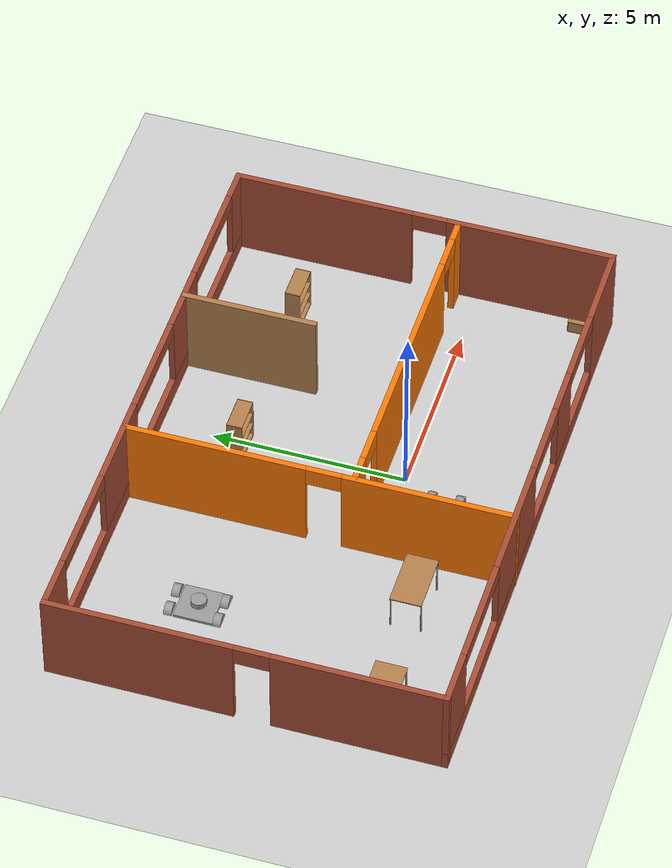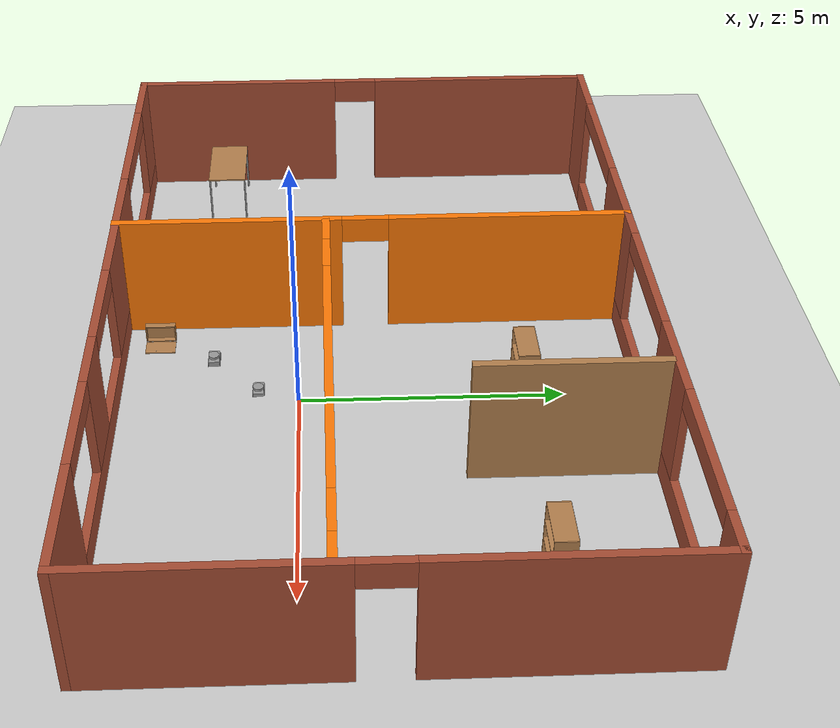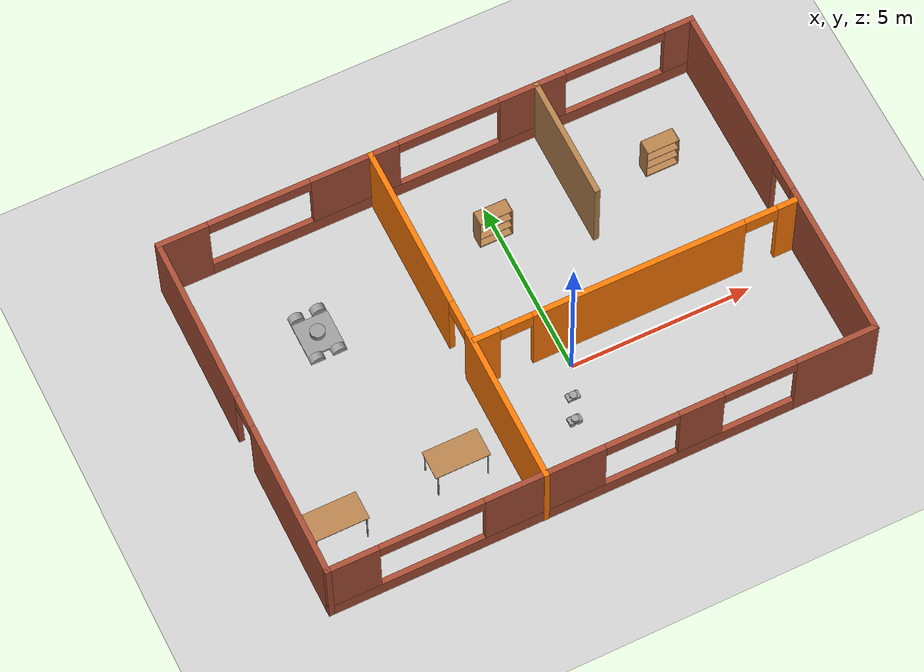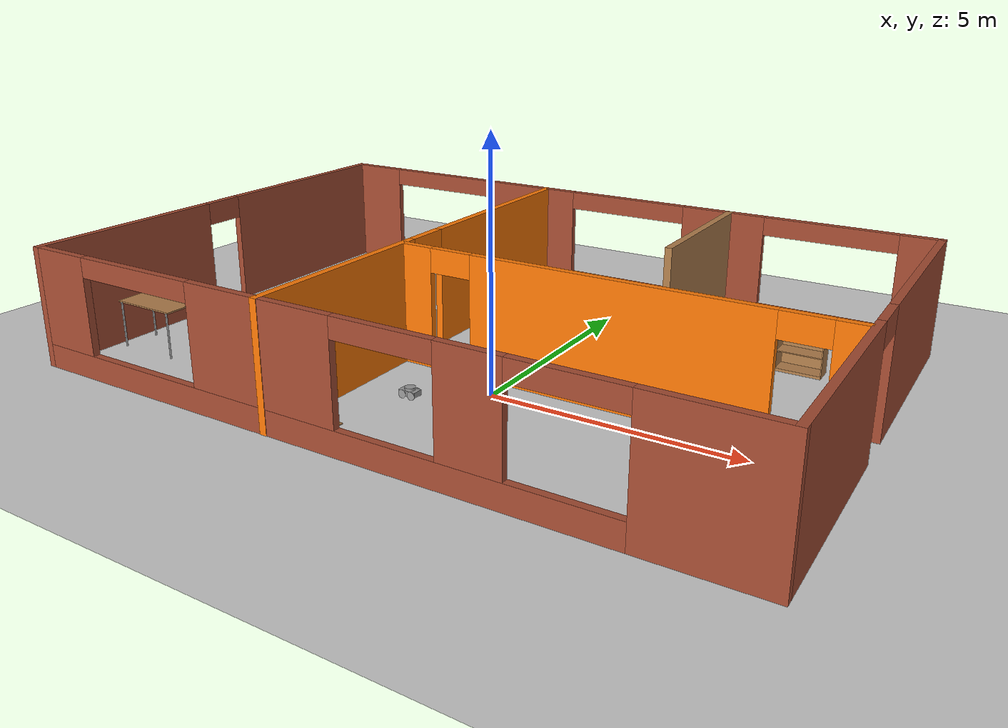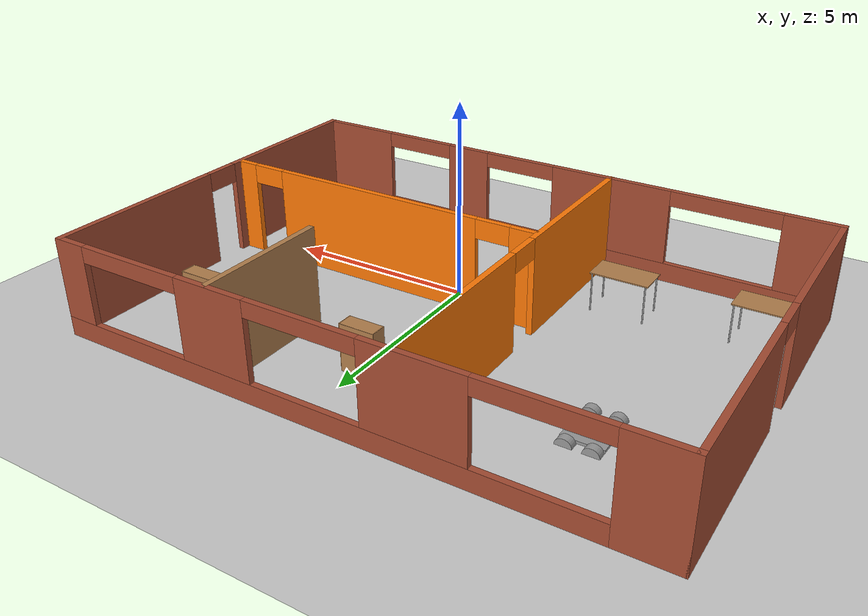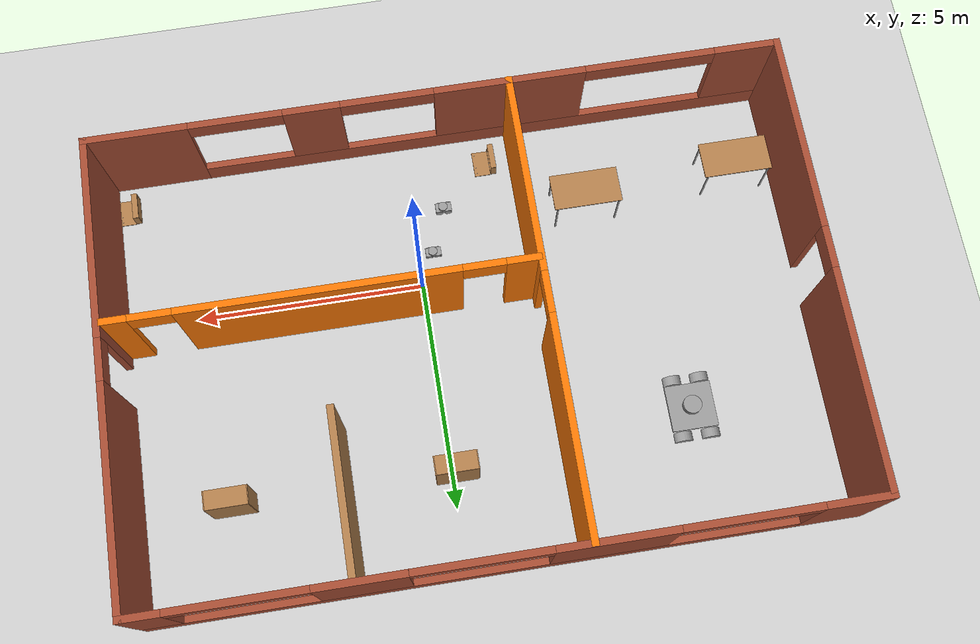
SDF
<sdf version="1.6">
 <world name="default">
  <plugin name="welcome message" filename="libwelcome_message.so"/>
  <light name="sun" type="directional">
   <pose>0 0 10 0 -0 0</pose>
   <diffuse>0.8 0.8 0.8 1</diffuse>
   <specular>0.2 0.2 0.2 1</specular>
   <attenuation>
    <range>1000</range>
    <constant>0.9</constant>
    <linear>0.01</linear>
    <quadratic>0.001</quadratic>
   </attenuation>
   <direction>-0.5 0.1 -0.9</direction>
  </light>
  <model name="ground_plane">
   <static>1</static>
   <link name="link">
    <collision name="collision">
     <geometry><plane><normal>0 0 1</normal><size>100 100</size></plane></geometry>
     <surface><friction><ode><mu>100</mu><mu2>50</mu2></ode></friction></surface>
    </collision>
    <visual name="visual">
     <cast_shadows>0</cast_shadows>
     <geometry><plane><normal>0 0 1</normal><size>100 100</size></plane></geometry>
     <material>
      <script><uri>file://media/materials/scripts/gazebo.material</uri><name>Gazebo/Grey</name></script>
     </material>
    </visual>
   </link>
  </model>
  <gravity>0 0 -9.8</gravity>
  <magnetic_field>6e-06 2.3e-05 -4.2e-05</magnetic_field>
  <atmosphere type="adiabatic"/>
  <physics name="default_physics" default="0" type="ode">
   <max_step_size>0.001</max_step_size>
   <real_time_factor>1</real_time_factor>
   <real_time_update_rate>1000</real_time_update_rate>
  </physics>
  <scene><ambient>0.4 0.4 0.4 1</ambient><background>0.7 0.7 0.7 1</background><shadows>1</shadows></scene>
  <spherical_coordinates>
   <surface_model>EARTH_WGS84</surface_model>
   <latitude_deg>0</latitude_deg>
   <longitude_deg>0</longitude_deg>
   <elevation>0</elevation>
   <heading_deg>0</heading_deg>
  </spherical_coordinates>
  <model name="Recon01">
   <link name="link_0">
    <pose>-0.001667 -0.001667 0 0 -0 0</pose>
    <inertial>
     <mass>1</mass>
     <inertia>
      <ixx>0.166667</ixx>
      <ixy>0</ixy>
      <ixz>0</ixz>
      <iyy>0.166667</iyy>
      <iyz>0</iyz>
      <izz>0.166667</izz>
     </inertia>
    </inertial>
    <visual name="visual">
     <geometry><box><size>0.35 0.2 0.1</size></box></geometry>
     <material>
      <lighting>1</lighting>
      <script><uri>file://media/materials/scripts/gazebo.material</uri><name>Gazebo/Grey</name></script>
      <ambient>0.3 0.3 0.3 1</ambient>
      <diffuse>0.7 0.7 0.7 1</diffuse>
      <specular>0.01 0.01 0.01 1</specular>
      <emissive>0 0 0 1</emissive>
      <shader type="vertex"><normal_map>__default__</normal_map></shader>
     </material>
    </visual>
    <collision name="collision">
     <geometry><box><size>0.35 0.2 0.1</size></box></geometry>
     <surface>
      <friction>
       <ode><mu>1</mu><mu2>1</mu2><fdir1>0 0 0</fdir1><slip1>0</slip1><slip2>0</slip2></ode>
       <torsional>
        <coefficient>1</coefficient>
        <patch_radius>0</patch_radius>
        <surface_radius>0</surface_radius>
        <use_patch_radius>1</use_patch_radius>
        <ode><slip>0</slip></ode>
       </torsional>
      </friction>
      <bounce><restitution_coefficient>0</restitution_coefficient><threshold>1e+06</threshold></bounce>
      <contact>
       <collide_without_contact>0</collide_without_contact>
       <collide_without_contact_bitmask>1</collide_without_contact_bitmask>
       <collide_bitmask>1</collide_bitmask>
       <ode>
        <soft_cfm>0</soft_cfm>
        <soft_erp>0.2</soft_erp>
        <kp>1e+13</kp>
        <kd>1</kd>
        <max_vel>0.01</max_vel>
        <min_depth>0</min_depth>
       </ode>
       <bullet>
        <split_impulse>1</split_impulse>
        <split_impulse_penetration_threshold>-0.01</split_impulse_penetration_threshold>
        <soft_cfm>0</soft_cfm>
        <soft_erp>0.2</soft_erp>
        <kp>1e+13</kp>
        <kd>1</kd>
       </bullet>
      </contact>
     </surface>
    </collision>
   </link>
   <link name="link_1">
    <pose>-0.096667 0.108333 -0.02 1.5708 -0 0</pose>
    <inertial>
     <mass>1</mass>
     <inertia><ixx>0.145833</ixx><ixy>0</ixy><ixz>0</ixz><iyy>0.145833</iyy><iyz>0</iyz><izz>0.125</izz></inertia>
    </inertial>
    <visual name="visual">
     <geometry><cylinder><radius>0.08</radius><length>0.01</length></cylinder></geometry>
     <material>
      <lighting>1</lighting>
      <script><uri>file://media/materials/scripts/gazebo.material</uri><name>Gazebo/Grey</name></script>
      <ambient>0.3 0.3 0.3 1</ambient>
      <diffuse>0.7 0.7 0.7 1</diffuse>
      <specular>0.01 0.01 0.01 1</specular>
      <emissive>0 0 0 1</emissive>
      <shader type="vertex"><normal_map>__default__</normal_map></shader>
     </material>
    </visual>
    <collision name="collision">
     <geometry><cylinder><radius>0.08</radius><length>0.01</length></cylinder></geometry>
     <surface>
      <friction>
       <ode><mu>1</mu><mu2>1</mu2><fdir1>0 0 0</fdir1><slip1>0</slip1><slip2>0</slip2></ode>
       <torsional>
        <coefficient>1</coefficient>
        <patch_radius>0</patch_radius>
        <surface_radius>0</surface_radius>
        <use_patch_radius>1</use_patch_radius>
        <ode><slip>0</slip></ode>
       </torsional>
      </friction>
      <bounce><restitution_coefficient>0</restitution_coefficient><threshold>1e+06</threshold></bounce>
      <contact>
       <collide_without_contact>0</collide_without_contact>
       <collide_without_contact_bitmask>1</collide_without_contact_bitmask>
       <collide_bitmask>1</collide_bitmask>
       <ode>
        <soft_cfm>0</soft_cfm>
        <soft_erp>0.2</soft_erp>
        <kp>1e+13</kp>
        <kd>1</kd>
        <max_vel>0.01</max_vel>
        <min_depth>0</min_depth>
       </ode>
       <bullet>
        <split_impulse>1</split_impulse>
        <split_impulse_penetration_threshold>-0.01</split_impulse_penetration_threshold>
        <soft_cfm>0</soft_cfm>
        <soft_erp>0.2</soft_erp>
        <kp>1e+13</kp>
        <kd>1</kd>
       </bullet>
      </contact>
     </surface>
    </collision>
   </link>
   <link name="link_1_clone">
    <pose>0.093333 0.108333 -0.02 1.5708 -0 0</pose>
    <inertial>
     <mass>1</mass>
     <inertia><ixx>0.145833</ixx><ixy>0</ixy><ixz>0</ixz><iyy>0.145833</iyy><iyz>0</iyz><izz>0.125</izz></inertia>
    </inertial>
    <visual name="visual">
     <geometry><cylinder><radius>0.08</radius><length>0.01</length></cylinder></geometry>
     <material>
      <lighting>1</lighting>
      <script><uri>file://media/materials/scripts/gazebo.material</uri><name>Gazebo/Grey</name></script>
      <ambient>0.3 0.3 0.3 1</ambient>
      <diffuse>0.7 0.7 0.7 1</diffuse>
      <specular>0.01 0.01 0.01 1</specular>
      <emissive>0 0 0 1</emissive>
      <shader type="vertex"><normal_map>__default__</normal_map></shader>
     </material>
    </visual>
    <collision name="collision">
     <geometry><cylinder><radius>0.08</radius><length>0.01</length></cylinder></geometry>
     <surface>
      <friction>
       <ode><mu>1</mu><mu2>1</mu2><fdir1>0 0 0</fdir1><slip1>0</slip1><slip2>0</slip2></ode>
       <torsional>
        <coefficient>1</coefficient>
        <patch_radius>0</patch_radius>
        <surface_radius>0</surface_radius>
        <use_patch_radius>1</use_patch_radius>
        <ode><slip>0</slip></ode>
       </torsional>
      </friction>
      <bounce><restitution_coefficient>0</restitution_coefficient><threshold>1e+06</threshold></bounce>
      <contact>
       <collide_without_contact>0</collide_without_contact>
       <collide_without_contact_bitmask>1</collide_without_contact_bitmask>
       <collide_bitmask>1</collide_bitmask>
       <ode>
        <soft_cfm>0</soft_cfm>
        <soft_erp>0.2</soft_erp>
        <kp>1e+13</kp>
        <kd>1</kd>
        <max_vel>0.01</max_vel>
        <min_depth>0</min_depth>
       </ode>
       <bullet>
        <split_impulse>1</split_impulse>
        <split_impulse_penetration_threshold>-0.01</split_impulse_penetration_threshold>
        <soft_cfm>0</soft_cfm>
        <soft_erp>0.2</soft_erp>
        <kp>1e+13</kp>
        <kd>1</kd>
       </bullet>
      </contact>
     </surface>
    </collision>
   </link>
   <link name="link_1_clone_0">
    <pose>-0.096667 -0.106667 -0.02 1.5708 -0 0</pose>
    <inertial>
     <mass>1</mass>
     <inertia><ixx>0.145833</ixx><ixy>0</ixy><ixz>0</ixz><iyy>0.145833</iyy><iyz>0</iyz><izz>0.125</izz></inertia>
    </inertial>
    <visual name="visual">
     <geometry><cylinder><radius>0.08</radius><length>0.01</length></cylinder></geometry>
     <material>
      <lighting>1</lighting>
      <script><uri>file://media/materials/scripts/gazebo.material</uri><name>Gazebo/Grey</name></script>
      <ambient>0.3 0.3 0.3 1</ambient>
      <diffuse>0.7 0.7 0.7 1</diffuse>
      <specular>0.01 0.01 0.01 1</specular>
      <emissive>0 0 0 1</emissive>
      <shader type="vertex"><normal_map>__default__</normal_map></shader>
     </material>
    </visual>
    <collision name="collision">
     <geometry><cylinder><radius>0.08</radius><length>0.01</length></cylinder></geometry>
     <surface>
      <friction>
       <ode><mu>1</mu><mu2>1</mu2><fdir1>0 0 0</fdir1><slip1>0</slip1><slip2>0</slip2></ode>
       <torsional>
        <coefficient>1</coefficient>
        <patch_radius>0</patch_radius>
        <surface_radius>0</surface_radius>
        <use_patch_radius>1</use_patch_radius>
        <ode><slip>0</slip></ode>
       </torsional>
      </friction>
      <bounce><restitution_coefficient>0</restitution_coefficient><threshold>1e+06</threshold></bounce>
      <contact>
       <collide_without_contact>0</collide_without_contact>
       <collide_without_contact_bitmask>1</collide_without_contact_bitmask>
       <collide_bitmask>1</collide_bitmask>
       <ode>
        <soft_cfm>0</soft_cfm>
        <soft_erp>0.2</soft_erp>
        <kp>1e+13</kp>
        <kd>1</kd>
        <max_vel>0.01</max_vel>
        <min_depth>0</min_depth>
       </ode>
       <bullet>
        <split_impulse>1</split_impulse>
        <split_impulse_penetration_threshold>-0.01</split_impulse_penetration_threshold>
        <soft_cfm>0</soft_cfm>
        <soft_erp>0.2</soft_erp>
        <kp>1e+13</kp>
        <kd>1</kd>
       </bullet>
      </contact>
     </surface>
    </collision>
   </link>
   <link name="link_1_clone_1">
    <pose>0.093333 -0.106667 -0.02 1.5708 -0 0</pose>
    <inertial>
     <mass>1</mass>
     <inertia><ixx>0.145833</ixx><ixy>0</ixy><ixz>0</ixz><iyy>0.145833</iyy><iyz>0</iyz><izz>0.125</izz></inertia>
    </inertial>
    <visual name="visual">
     <geometry><cylinder><radius>0.08</radius><length>0.01</length></cylinder></geometry>
     <material>
      <lighting>1</lighting>
      <script><uri>file://media/materials/scripts/gazebo.material</uri><name>Gazebo/Grey</name></script>
      <ambient>0.3 0.3 0.3 1</ambient>
      <diffuse>0.7 0.7 0.7 1</diffuse>
      <specular>0.01 0.01 0.01 1</specular>
      <emissive>0 0 0 1</emissive>
      <shader type="vertex"><normal_map>__default__</normal_map></shader>
     </material>
    </visual>
    <collision name="collision">
     <geometry><cylinder><radius>0.08</radius><length>0.01</length></cylinder></geometry>
     <surface>
      <friction>
       <ode><mu>1</mu><mu2>1</mu2><fdir1>0 0 0</fdir1><slip1>0</slip1><slip2>0</slip2></ode>
       <torsional>
        <coefficient>1</coefficient>
        <patch_radius>0</patch_radius>
        <surface_radius>0</surface_radius>
        <use_patch_radius>1</use_patch_radius>
        <ode><slip>0</slip></ode>
       </torsional>
      </friction>
      <bounce><restitution_coefficient>0</restitution_coefficient><threshold>1e+06</threshold></bounce>
      <contact>
       <collide_without_contact>0</collide_without_contact>
       <collide_without_contact_bitmask>1</collide_without_contact_bitmask>
       <collide_bitmask>1</collide_bitmask>
       <ode>
        <soft_cfm>0</soft_cfm>
        <soft_erp>0.2</soft_erp>
        <kp>1e+13</kp>
        <kd>1</kd>
        <max_vel>0.01</max_vel>
        <min_depth>0</min_depth>
       </ode>
       <bullet>
        <split_impulse>1</split_impulse>
        <split_impulse_penetration_threshold>-0.01</split_impulse_penetration_threshold>
        <soft_cfm>0</soft_cfm>
        <soft_erp>0.2</soft_erp>
        <kp>1e+13</kp>
        <kd>1</kd>
       </bullet>
      </contact>
     </surface>
    </collision>
   </link>
   <link name="link_2">
    <pose>0.008333 -0.001667 0.08 0 -0 0</pose>
    <inertial>
     <mass>1</mass>
     <inertia><ixx>0.145833</ixx><ixy>0</ixy><ixz>0</ixz><iyy>0.145833</iyy><iyz>0</iyz><izz>0.125</izz></inertia>
    </inertial>
    <visual name="visual">
     <geometry><cylinder><radius>0.1</radius><length>0.05</length></cylinder></geometry>
     <material>
      <lighting>1</lighting>
      <script><uri>file://media/materials/scripts/gazebo.material</uri><name>Gazebo/Grey</name></script>
      <ambient>0.3 0.3 0.3 1</ambient>
      <diffuse>0.7 0.7 0.7 1</diffuse>
      <specular>0.01 0.01 0.01 1</specular>
      <emissive>0 0 0 1</emissive>
      <shader type="vertex"><normal_map>__default__</normal_map></shader>
     </material>
    </visual>
    <collision name="collision">
     <geometry><cylinder><radius>0.08</radius><length>0.05</length></cylinder></geometry>
     <surface>
      <friction>
       <ode><mu>1</mu><mu2>1</mu2><fdir1>0 0 0</fdir1><slip1>0</slip1><slip2>0</slip2></ode>
       <torsional>
        <coefficient>1</coefficient>
        <patch_radius>0</patch_radius>
        <surface_radius>0</surface_radius>
        <use_patch_radius>1</use_patch_radius>
        <ode><slip>0</slip></ode>
       </torsional>
      </friction>
      <bounce><restitution_coefficient>0</restitution_coefficient><threshold>1e+06</threshold></bounce>
      <contact>
       <collide_without_contact>0</collide_without_contact>
       <collide_without_contact_bitmask>1</collide_without_contact_bitmask>
       <collide_bitmask>1</collide_bitmask>
       <ode>
        <soft_cfm>0</soft_cfm>
        <soft_erp>0.2</soft_erp>
        <kp>1e+13</kp>
        <kd>1</kd>
        <max_vel>0.01</max_vel>
        <min_depth>0</min_depth>
       </ode>
       <bullet>
        <split_impulse>1</split_impulse>
        <split_impulse_penetration_threshold>-0.01</split_impulse_penetration_threshold>
        <soft_cfm>0</soft_cfm>
        <soft_erp>0.2</soft_erp>
        <kp>1e+13</kp>
        <kd>1</kd>
       </bullet>
      </contact>
     </surface>
    </collision>
   </link>
   <joint name="link_0_JOINT_10" type="revolute">
    <parent>link_0</parent>
    <child>link_2</child>
    <axis>
     <xyz>1 0 0</xyz>
     <use_parent_model_frame>0</use_parent_model_frame>
     <limit>
      <lower>-1.79769e+308</lower>
      <upper>1.79769e+308</upper>
      <effort>-1</effort>
      <velocity>-1</velocity>
     </limit>
     <dynamics>
      <spring_reference>0</spring_reference>
      <spring_stiffness>0</spring_stiffness>
      <damping>0</damping>
     </dynamics>
    </axis>
    <physics>
     <ode><limit><cfm>0</cfm><erp>0.2</erp></limit><suspension><cfm>0</cfm><erp>0.2</erp></suspension></ode>
    </physics>
   </joint>
   <joint name="link_0_JOINT_2" type="revolute">
    <parent>link_0</parent>
    <child>link_1_clone_1</child>
    <axis>
     <xyz>1 0 0</xyz>
     <use_parent_model_frame>0</use_parent_model_frame>
     <limit>
      <lower>-1.79769e+308</lower>
      <upper>1.79769e+308</upper>
      <effort>-1</effort>
      <velocity>-1</velocity>
     </limit>
     <dynamics>
      <spring_reference>0</spring_reference>
      <spring_stiffness>0</spring_stiffness>
      <damping>0</damping>
      <friction>0</friction>
     </dynamics>
    </axis>
    <physics>
     <ode><limit><cfm>0</cfm><erp>0.2</erp></limit><suspension><cfm>0</cfm><erp>0.2</erp></suspension></ode>
    </physics>
   </joint>
   <joint name="link_0_JOINT_3" type="revolute">
    <parent>link_0</parent>
    <child>link_1_clone_0</child>
    <axis>
     <xyz>1 0 0</xyz>
     <use_parent_model_frame>0</use_parent_model_frame>
     <limit>
      <lower>-1.79769e+308</lower>
      <upper>1.79769e+308</upper>
      <effort>-1</effort>
      <velocity>-1</velocity>
     </limit>
     <dynamics>
      <spring_reference>0</spring_reference>
      <spring_stiffness>0</spring_stiffness>
      <damping>0</damping>
     </dynamics>
    </axis>
    <physics>
     <ode><limit><cfm>0</cfm><erp>0.2</erp></limit><suspension><cfm>0</cfm><erp>0.2</erp></suspension></ode>
    </physics>
   </joint>
   <joint name="link_0_JOINT_8" type="revolute">
    <parent>link_0</parent>
    <child>link_1_clone</child>
    <axis>
     <xyz>1 0 0</xyz>
     <use_parent_model_frame>0</use_parent_model_frame>
     <limit>
      <lower>-1.79769e+308</lower>
      <upper>1.79769e+308</upper>
      <effort>-1</effort>
      <velocity>-1</velocity>
     </limit>
     <dynamics>
      <spring_reference>0</spring_reference>
      <spring_stiffness>0</spring_stiffness>
      <damping>0</damping>
     </dynamics>
    </axis>
    <physics>
     <ode><limit><cfm>0</cfm><erp>0.2</erp></limit><suspension><cfm>0</cfm><erp>0.2</erp></suspension></ode>
    </physics>
   </joint>
   <joint name="link_0_JOINT_9" type="revolute">
    <parent>link_0</parent>
    <child>link_1</child>
    <axis>
     <xyz>1 0 0</xyz>
     <use_parent_model_frame>0</use_parent_model_frame>
     <limit>
      <lower>-1.79769e+308</lower>
      <upper>1.79769e+308</upper>
      <effort>-1</effort>
      <velocity>-1</velocity>
     </limit>
     <dynamics>
      <spring_reference>0</spring_reference>
      <spring_stiffness>0</spring_stiffness>
      <damping>0</damping>
     </dynamics>
    </axis>
    <physics>
     <ode><limit><cfm>0</cfm><erp>0.2</erp></limit><suspension><cfm>0</cfm><erp>0.2</erp></suspension></ode>
    </physics>
   </joint>
   <static>0</static>
   <pose>-0.714552 -1.58603 0.5 0 -0 0</pose>
  </model>
  <model name="Recon01_0">
   <link name="link_0">
    <pose>-0.001667 -0.001667 0 0 -0 0</pose>
    <inertial>
     <mass>1</mass>
     <inertia>
      <ixx>0.166667</ixx>
      <ixy>0</ixy>
      <ixz>0</ixz>
      <iyy>0.166667</iyy>
      <iyz>0</iyz>
      <izz>0.166667</izz>
     </inertia>
    </inertial>
    <visual name="visual">
     <geometry><box><size>0.35 0.2 0.1</size></box></geometry>
     <material>
      <lighting>1</lighting>
      <script><uri>file://media/materials/scripts/gazebo.material</uri><name>Gazebo/Grey</name></script>
      <ambient>0.3 0.3 0.3 1</ambient>
      <diffuse>0.7 0.7 0.7 1</diffuse>
      <specular>0.01 0.01 0.01 1</specular>
      <emissive>0 0 0 1</emissive>
      <shader type="vertex"><normal_map>__default__</normal_map></shader>
     </material>
    </visual>
    <collision name="collision">
     <geometry><box><size>0.35 0.2 0.1</size></box></geometry>
     <surface>
      <friction>
       <ode><mu>1</mu><mu2>1</mu2><fdir1>0 0 0</fdir1><slip1>0</slip1><slip2>0</slip2></ode>
       <torsional>
        <coefficient>1</coefficient>
        <patch_radius>0</patch_radius>
        <surface_radius>0</surface_radius>
        <use_patch_radius>1</use_patch_radius>
        <ode><slip>0</slip></ode>
       </torsional>
      </friction>
      <bounce><restitution_coefficient>0</restitution_coefficient><threshold>1e+06</threshold></bounce>
      <contact>
       <collide_without_contact>0</collide_without_contact>
       <collide_without_contact_bitmask>1</collide_without_contact_bitmask>
       <collide_bitmask>1</collide_bitmask>
       <ode>
        <soft_cfm>0</soft_cfm>
        <soft_erp>0.2</soft_erp>
        <kp>1e+13</kp>
        <kd>1</kd>
        <max_vel>0.01</max_vel>
        <min_depth>0</min_depth>
       </ode>
       <bullet>
        <split_impulse>1</split_impulse>
        <split_impulse_penetration_threshold>-0.01</split_impulse_penetration_threshold>
        <soft_cfm>0</soft_cfm>
        <soft_erp>0.2</soft_erp>
        <kp>1e+13</kp>
        <kd>1</kd>
       </bullet>
      </contact>
     </surface>
    </collision>
   </link>
   <link name="link_1">
    <pose>-0.096667 0.108333 -0.02 1.5708 -0 0</pose>
    <inertial>
     <mass>1</mass>
     <inertia><ixx>0.145833</ixx><ixy>0</ixy><ixz>0</ixz><iyy>0.145833</iyy><iyz>0</iyz><izz>0.125</izz></inertia>
    </inertial>
    <visual name="visual">
     <geometry><cylinder><radius>0.08</radius><length>0.01</length></cylinder></geometry>
     <material>
      <lighting>1</lighting>
      <script><uri>file://media/materials/scripts/gazebo.material</uri><name>Gazebo/Grey</name></script>
      <ambient>0.3 0.3 0.3 1</ambient>
      <diffuse>0.7 0.7 0.7 1</diffuse>
      <specular>0.01 0.01 0.01 1</specular>
      <emissive>0 0 0 1</emissive>
      <shader type="vertex"><normal_map>__default__</normal_map></shader>
     </material>
    </visual>
    <collision name="collision">
     <geometry><cylinder><radius>0.08</radius><length>0.01</length></cylinder></geometry>
     <surface>
      <friction>
       <ode><mu>1</mu><mu2>1</mu2><fdir1>0 0 0</fdir1><slip1>0</slip1><slip2>0</slip2></ode>
       <torsional>
        <coefficient>1</coefficient>
        <patch_radius>0</patch_radius>
        <surface_radius>0</surface_radius>
        <use_patch_radius>1</use_patch_radius>
        <ode><slip>0</slip></ode>
       </torsional>
      </friction>
      <bounce><restitution_coefficient>0</restitution_coefficient><threshold>1e+06</threshold></bounce>
      <contact>
       <collide_without_contact>0</collide_without_contact>
       <collide_without_contact_bitmask>1</collide_without_contact_bitmask>
       <collide_bitmask>1</collide_bitmask>
       <ode>
        <soft_cfm>0</soft_cfm>
        <soft_erp>0.2</soft_erp>
        <kp>1e+13</kp>
        <kd>1</kd>
        <max_vel>0.01</max_vel>
        <min_depth>0</min_depth>
       </ode>
       <bullet>
        <split_impulse>1</split_impulse>
        <split_impulse_penetration_threshold>-0.01</split_impulse_penetration_threshold>
        <soft_cfm>0</soft_cfm>
        <soft_erp>0.2</soft_erp>
        <kp>1e+13</kp>
        <kd>1</kd>
       </bullet>
      </contact>
     </surface>
    </collision>
   </link>
   <link name="link_1_clone">
    <pose>0.093333 0.108333 -0.02 1.5708 -0 0</pose>
    <inertial>
     <mass>1</mass>
     <inertia><ixx>0.145833</ixx><ixy>0</ixy><ixz>0</ixz><iyy>0.145833</iyy><iyz>0</iyz><izz>0.125</izz></inertia>
    </inertial>
    <visual name="visual">
     <geometry><cylinder><radius>0.08</radius><length>0.01</length></cylinder></geometry>
     <material>
      <lighting>1</lighting>
      <script><uri>file://media/materials/scripts/gazebo.material</uri><name>Gazebo/Grey</name></script>
      <ambient>0.3 0.3 0.3 1</ambient>
      <diffuse>0.7 0.7 0.7 1</diffuse>
      <specular>0.01 0.01 0.01 1</specular>
      <emissive>0 0 0 1</emissive>
      <shader type="vertex"><normal_map>__default__</normal_map></shader>
     </material>
    </visual>
    <collision name="collision">
     <geometry><cylinder><radius>0.08</radius><length>0.01</length></cylinder></geometry>
     <surface>
      <friction>
       <ode><mu>1</mu><mu2>1</mu2><fdir1>0 0 0</fdir1><slip1>0</slip1><slip2>0</slip2></ode>
       <torsional>
        <coefficient>1</coefficient>
        <patch_radius>0</patch_radius>
        <surface_radius>0</surface_radius>
        <use_patch_radius>1</use_patch_radius>
        <ode><slip>0</slip></ode>
       </torsional>
      </friction>
      <bounce><restitution_coefficient>0</restitution_coefficient><threshold>1e+06</threshold></bounce>
      <contact>
       <collide_without_contact>0</collide_without_contact>
       <collide_without_contact_bitmask>1</collide_without_contact_bitmask>
       <collide_bitmask>1</collide_bitmask>
       <ode>
        <soft_cfm>0</soft_cfm>
        <soft_erp>0.2</soft_erp>
        <kp>1e+13</kp>
        <kd>1</kd>
        <max_vel>0.01</max_vel>
        <min_depth>0</min_depth>
       </ode>
       <bullet>
        <split_impulse>1</split_impulse>
        <split_impulse_penetration_threshold>-0.01</split_impulse_penetration_threshold>
        <soft_cfm>0</soft_cfm>
        <soft_erp>0.2</soft_erp>
        <kp>1e+13</kp>
        <kd>1</kd>
       </bullet>
      </contact>
     </surface>
    </collision>
   </link>
   <link name="link_1_clone_0">
    <pose>-0.096667 -0.106667 -0.02 1.5708 -0 0</pose>
    <inertial>
     <mass>1</mass>
     <inertia><ixx>0.145833</ixx><ixy>0</ixy><ixz>0</ixz><iyy>0.145833</iyy><iyz>0</iyz><izz>0.125</izz></inertia>
    </inertial>
    <visual name="visual">
     <geometry><cylinder><radius>0.08</radius><length>0.01</length></cylinder></geometry>
     <material>
      <lighting>1</lighting>
      <script><uri>file://media/materials/scripts/gazebo.material</uri><name>Gazebo/Grey</name></script>
      <ambient>0.3 0.3 0.3 1</ambient>
      <diffuse>0.7 0.7 0.7 1</diffuse>
      <specular>0.01 0.01 0.01 1</specular>
      <emissive>0 0 0 1</emissive>
      <shader type="vertex"><normal_map>__default__</normal_map></shader>
     </material>
    </visual>
    <collision name="collision">
     <geometry><cylinder><radius>0.08</radius><length>0.01</length></cylinder></geometry>
     <surface>
      <friction>
       <ode><mu>1</mu><mu2>1</mu2><fdir1>0 0 0</fdir1><slip1>0</slip1><slip2>0</slip2></ode>
       <torsional>
        <coefficient>1</coefficient>
        <patch_radius>0</patch_radius>
        <surface_radius>0</surface_radius>
        <use_patch_radius>1</use_patch_radius>
        <ode><slip>0</slip></ode>
       </torsional>
      </friction>
      <bounce><restitution_coefficient>0</restitution_coefficient><threshold>1e+06</threshold></bounce>
      <contact>
       <collide_without_contact>0</collide_without_contact>
       <collide_without_contact_bitmask>1</collide_without_contact_bitmask>
       <collide_bitmask>1</collide_bitmask>
       <ode>
        <soft_cfm>0</soft_cfm>
        <soft_erp>0.2</soft_erp>
        <kp>1e+13</kp>
        <kd>1</kd>
        <max_vel>0.01</max_vel>
        <min_depth>0</min_depth>
       </ode>
       <bullet>
        <split_impulse>1</split_impulse>
        <split_impulse_penetration_threshold>-0.01</split_impulse_penetration_threshold>
        <soft_cfm>0</soft_cfm>
        <soft_erp>0.2</soft_erp>
        <kp>1e+13</kp>
        <kd>1</kd>
       </bullet>
      </contact>
     </surface>
    </collision>
   </link>
   <link name="link_1_clone_1">
    <pose>0.093333 -0.106667 -0.02 1.5708 -0 0</pose>
    <inertial>
     <mass>1</mass>
     <inertia><ixx>0.145833</ixx><ixy>0</ixy><ixz>0</ixz><iyy>0.145833</iyy><iyz>0</iyz><izz>0.125</izz></inertia>
    </inertial>
    <visual name="visual">
     <geometry><cylinder><radius>0.08</radius><length>0.01</length></cylinder></geometry>
     <material>
      <lighting>1</lighting>
      <script><uri>file://media/materials/scripts/gazebo.material</uri><name>Gazebo/Grey</name></script>
      <ambient>0.3 0.3 0.3 1</ambient>
      <diffuse>0.7 0.7 0.7 1</diffuse>
      <specular>0.01 0.01 0.01 1</specular>
      <emissive>0 0 0 1</emissive>
      <shader type="vertex"><normal_map>__default__</normal_map></shader>
     </material>
    </visual>
    <collision name="collision">
     <geometry><cylinder><radius>0.08</radius><length>0.01</length></cylinder></geometry>
     <surface>
      <friction>
       <ode><mu>1</mu><mu2>1</mu2><fdir1>0 0 0</fdir1><slip1>0</slip1><slip2>0</slip2></ode>
       <torsional>
        <coefficient>1</coefficient>
        <patch_radius>0</patch_radius>
        <surface_radius>0</surface_radius>
        <use_patch_radius>1</use_patch_radius>
        <ode><slip>0</slip></ode>
       </torsional>
      </friction>
      <bounce><restitution_coefficient>0</restitution_coefficient><threshold>1e+06</threshold></bounce>
      <contact>
       <collide_without_contact>0</collide_without_contact>
       <collide_without_contact_bitmask>1</collide_without_contact_bitmask>
       <collide_bitmask>1</collide_bitmask>
       <ode>
        <soft_cfm>0</soft_cfm>
        <soft_erp>0.2</soft_erp>
        <kp>1e+13</kp>
        <kd>1</kd>
        <max_vel>0.01</max_vel>
        <min_depth>0</min_depth>
       </ode>
       <bullet>
        <split_impulse>1</split_impulse>
        <split_impulse_penetration_threshold>-0.01</split_impulse_penetration_threshold>
        <soft_cfm>0</soft_cfm>
        <soft_erp>0.2</soft_erp>
        <kp>1e+13</kp>
        <kd>1</kd>
       </bullet>
      </contact>
     </surface>
    </collision>
   </link>
   <link name="link_2">
    <pose>0.008333 -0.001667 0.08 0 -0 0</pose>
    <inertial>
     <mass>1</mass>
     <inertia><ixx>0.145833</ixx><ixy>0</ixy><ixz>0</ixz><iyy>0.145833</iyy><iyz>0</iyz><izz>0.125</izz></inertia>
    </inertial>
    <visual name="visual">
     <geometry><cylinder><radius>0.1</radius><length>0.05</length></cylinder></geometry>
     <material>
      <lighting>1</lighting>
      <script><uri>file://media/materials/scripts/gazebo.material</uri><name>Gazebo/Grey</name></script>
      <ambient>0.3 0.3 0.3 1</ambient>
      <diffuse>0.7 0.7 0.7 1</diffuse>
      <specular>0.01 0.01 0.01 1</specular>
      <emissive>0 0 0 1</emissive>
      <shader type="vertex"><normal_map>__default__</normal_map></shader>
     </material>
    </visual>
    <collision name="collision">
     <geometry><cylinder><radius>0.08</radius><length>0.05</length></cylinder></geometry>
     <surface>
      <friction>
       <ode><mu>1</mu><mu2>1</mu2><fdir1>0 0 0</fdir1><slip1>0</slip1><slip2>0</slip2></ode>
       <torsional>
        <coefficient>1</coefficient>
        <patch_radius>0</patch_radius>
        <surface_radius>0</surface_radius>
        <use_patch_radius>1</use_patch_radius>
        <ode><slip>0</slip></ode>
       </torsional>
      </friction>
      <bounce><restitution_coefficient>0</restitution_coefficient><threshold>1e+06</threshold></bounce>
      <contact>
       <collide_without_contact>0</collide_without_contact>
       <collide_without_contact_bitmask>1</collide_without_contact_bitmask>
       <collide_bitmask>1</collide_bitmask>
       <ode>
        <soft_cfm>0</soft_cfm>
        <soft_erp>0.2</soft_erp>
        <kp>1e+13</kp>
        <kd>1</kd>
        <max_vel>0.01</max_vel>
        <min_depth>0</min_depth>
       </ode>
       <bullet>
        <split_impulse>1</split_impulse>
        <split_impulse_penetration_threshold>-0.01</split_impulse_penetration_threshold>
        <soft_cfm>0</soft_cfm>
        <soft_erp>0.2</soft_erp>
        <kp>1e+13</kp>
        <kd>1</kd>
       </bullet>
      </contact>
     </surface>
    </collision>
   </link>
   <joint name="link_0_JOINT_10" type="revolute">
    <parent>link_0</parent>
    <child>link_2</child>
    <axis>
     <xyz>1 0 0</xyz>
     <use_parent_model_frame>0</use_parent_model_frame>
     <limit>
      <lower>-1.79769e+308</lower>
      <upper>1.79769e+308</upper>
      <effort>-1</effort>
      <velocity>-1</velocity>
     </limit>
     <dynamics>
      <spring_reference>0</spring_reference>
      <spring_stiffness>0</spring_stiffness>
      <damping>0</damping>
     </dynamics>
    </axis>
    <physics>
     <ode><limit><cfm>0</cfm><erp>0.2</erp></limit><suspension><cfm>0</cfm><erp>0.2</erp></suspension></ode>
    </physics>
   </joint>
   <joint name="link_0_JOINT_2" type="revolute">
    <parent>link_0</parent>
    <child>link_1_clone_1</child>
    <axis>
     <xyz>1 0 0</xyz>
     <use_parent_model_frame>0</use_parent_model_frame>
     <limit>
      <lower>-1.79769e+308</lower>
      <upper>1.79769e+308</upper>
      <effort>-1</effort>
      <velocity>-1</velocity>
     </limit>
     <dynamics>
      <spring_reference>0</spring_reference>
      <spring_stiffness>0</spring_stiffness>
      <damping>0</damping>
      <friction>0</friction>
     </dynamics>
    </axis>
    <physics>
     <ode><limit><cfm>0</cfm><erp>0.2</erp></limit><suspension><cfm>0</cfm><erp>0.2</erp></suspension></ode>
    </physics>
   </joint>
   <joint name="link_0_JOINT_3" type="revolute">
    <parent>link_0</parent>
    <child>link_1_clone_0</child>
    <axis>
     <xyz>1 0 0</xyz>
     <use_parent_model_frame>0</use_parent_model_frame>
     <limit>
      <lower>-1.79769e+308</lower>
      <upper>1.79769e+308</upper>
      <effort>-1</effort>
      <velocity>-1</velocity>
     </limit>
     <dynamics>
      <spring_reference>0</spring_reference>
      <spring_stiffness>0</spring_stiffness>
      <damping>0</damping>
     </dynamics>
    </axis>
    <physics>
     <ode><limit><cfm>0</cfm><erp>0.2</erp></limit><suspension><cfm>0</cfm><erp>0.2</erp></suspension></ode>
    </physics>
   </joint>
   <joint name="link_0_JOINT_8" type="revolute">
    <parent>link_0</parent>
    <child>link_1_clone</child>
    <axis>
     <xyz>1 0 0</xyz>
     <use_parent_model_frame>0</use_parent_model_frame>
     <limit>
      <lower>-1.79769e+308</lower>
      <upper>1.79769e+308</upper>
      <effort>-1</effort>
      <velocity>-1</velocity>
     </limit>
     <dynamics>
      <spring_reference>0</spring_reference>
      <spring_stiffness>0</spring_stiffness>
      <damping>0</damping>
     </dynamics>
    </axis>
    <physics>
     <ode><limit><cfm>0</cfm><erp>0.2</erp></limit><suspension><cfm>0</cfm><erp>0.2</erp></suspension></ode>
    </physics>
   </joint>
   <joint name="link_0_JOINT_9" type="revolute">
    <parent>link_0</parent>
    <child>link_1</child>
    <axis>
     <xyz>1 0 0</xyz>
     <use_parent_model_frame>0</use_parent_model_frame>
     <limit>
      <lower>-1.79769e+308</lower>
      <upper>1.79769e+308</upper>
      <effort>-1</effort>
      <velocity>-1</velocity>
     </limit>
     <dynamics>
      <spring_reference>0</spring_reference>
      <spring_stiffness>0</spring_stiffness>
      <damping>0</damping>
     </dynamics>
    </axis>
    <physics>
     <ode><limit><cfm>0</cfm><erp>0.2</erp></limit><suspension><cfm>0</cfm><erp>0.2</erp></suspension></ode>
    </physics>
   </joint>
   <static>0</static>
   <pose>-0.350345 -0.762941 0 0 -0 0</pose>
  </model>
  <model name="Apartment">
   <pose>-0.845812 1.49022 0 0 -0 0</pose>
   <link name="Wall_10">
    <pose>0 4.92997 0 0 -0 0</pose>
    <visual name="Wall_10_Visual_0">
     <pose>-6.79371 0 1.25 0 -0 0</pose>
     <geometry><box><size>1.41257 0.15 2.5</size></box></geometry>
     <material>
      <script><uri>file://media/materials/scripts/gazebo.material</uri><name>Gazebo/Bricks</name></script>
      <ambient>1 1 1 1</ambient>
     </material>
     <meta><layer>0</layer></meta>
    </visual>
    <collision name="Wall_10_Collision_0">
     <geometry><box><size>1.41257 0.15 2.5</size></box></geometry>
     <pose>-6.79371 0 1.25 0 -0 0</pose>
    </collision>
    <visual name="Wall_10_Visual_1">
     <pose>0.706287 0 0.25 0 -0 0</pose>
     <geometry><box><size>13.5874 0.15 0.5</size></box></geometry>
     <material>
      <script><uri>file://media/materials/scripts/gazebo.material</uri><name>Gazebo/Bricks</name></script>
      <ambient>1 1 1 1</ambient>
     </material>
     <meta><layer>0</layer></meta>
    </visual>
    <collision name="Wall_10_Collision_1">
     <geometry><box><size>13.5874 0.15 0.5</size></box></geometry>
     <pose>0.706287 0 0.25 0 -0 0</pose>
    </collision>
    <visual name="Wall_10_Visual_2">
     <pose>-2.06392 0 1.5 0 -0 0</pose>
     <geometry><box><size>2.44702 0.15 2</size></box></geometry>
     <material>
      <script><uri>file://media/materials/scripts/gazebo.material</uri><name>Gazebo/Bricks</name></script>
      <ambient>1 1 1 1</ambient>
     </material>
     <meta><layer>0</layer></meta>
    </visual>
    <collision name="Wall_10_Collision_2">
     <geometry><box><size>2.44702 0.15 2</size></box></geometry>
     <pose>-2.06392 0 1.5 0 -0 0</pose>
    </collision>
    <visual name="Wall_10_Visual_3">
     <pose>2.89414 0 1.5 0 -0 0</pose>
     <geometry><box><size>1.86909 0.15 2</size></box></geometry>
     <material>
      <script><uri>file://media/materials/scripts/gazebo.material</uri><name>Gazebo/Bricks</name></script>
      <ambient>1 1 1 1</ambient>
     </material>
     <meta><layer>0</layer></meta>
    </visual>
    <collision name="Wall_10_Collision_3">
     <geometry><box><size>1.86909 0.15 2</size></box></geometry>
     <pose>2.89414 0 1.5 0 -0 0</pose>
    </collision>
    <visual name="Wall_10_Visual_4">
     <pose>7.06434 0 1.5 0 -0 0</pose>
     <geometry><box><size>0.87132 0.15 2</size></box></geometry>
     <material>
      <script><uri>file://media/materials/scripts/gazebo.material</uri><name>Gazebo/Bricks</name></script>
      <ambient>1 1 1 1</ambient>
     </material>
     <meta><layer>0</layer></meta>
    </visual>
    <collision name="Wall_10_Collision_4">
     <geometry><box><size>0.87132 0.15 2</size></box></geometry>
     <pose>7.06434 0 1.5 0 -0 0</pose>
    </collision>
    <visual name="Wall_10_Visual_5">
     <pose>-4.68743 0 2.3 0 -0 0</pose>
     <geometry><box><size>2.8 0.15 0.4</size></box></geometry>
     <material>
      <script><uri>file://media/materials/scripts/gazebo.material</uri><name>Gazebo/Bricks</name></script>
      <ambient>1 1 1 1</ambient>
     </material>
     <meta><layer>0</layer></meta>
    </visual>
    <collision name="Wall_10_Collision_5">
     <geometry><box><size>2.8 0.15 0.4</size></box></geometry>
     <pose>-4.68743 0 2.3 0 -0 0</pose>
    </collision>
    <visual name="Wall_10_Visual_6">
     <pose>0.559594 0 2.3 0 -0 0</pose>
     <geometry><box><size>2.8 0.15 0.4</size></box></geometry>
     <material>
      <script><uri>file://media/materials/scripts/gazebo.material</uri><name>Gazebo/Bricks</name></script>
      <ambient>1 1 1 1</ambient>
     </material>
     <meta><layer>0</layer></meta>
    </visual>
    <collision name="Wall_10_Collision_6">
     <geometry><box><size>2.8 0.15 0.4</size></box></geometry>
     <pose>0.559594 0 2.3 0 -0 0</pose>
    </collision>
    <visual name="Wall_10_Visual_7">
     <pose>5.22868 0 2.3 0 -0 0</pose>
     <geometry><box><size>2.8 0.15 0.4</size></box></geometry>
     <material>
      <script><uri>file://media/materials/scripts/gazebo.material</uri><name>Gazebo/Bricks</name></script>
      <ambient>1 1 1 1</ambient>
     </material>
     <meta><layer>0</layer></meta>
    </visual>
    <collision name="Wall_10_Collision_7">
     <geometry><box><size>2.8 0.15 0.4</size></box></geometry>
     <pose>5.22868 0 2.3 0 -0 0</pose>
    </collision>
   </link>
   <link name="Wall_11">
    <pose>7.425 0.004969 0 0 0 -1.5708</pose>
    <visual name="Wall_11_Visual_0">
     <pose>-2.65027 0 1.25 0 -0 0</pose>
     <geometry><box><size>4.69945 0.15 2.5</size></box></geometry>
     <material>
      <script><uri>file://media/materials/scripts/gazebo.material</uri><name>Gazebo/Bricks</name></script>
      <ambient>1 1 1 1</ambient>
     </material>
     <meta><layer>0</layer></meta>
    </visual>
    <collision name="Wall_11_Collision_0">
     <geometry><box><size>4.69945 0.15 2.5</size></box></geometry>
     <pose>-2.65027 0 1.25 0 -0 0</pose>
    </collision>
    <visual name="Wall_11_Visual_1">
     <pose>2.79973 0 1.25 0 -0 0</pose>
     <geometry><box><size>4.40055 0.15 2.5</size></box></geometry>
     <material>
      <script><uri>file://media/materials/scripts/gazebo.material</uri><name>Gazebo/Bricks</name></script>
      <ambient>1 1 1 1</ambient>
     </material>
     <meta><layer>0</layer></meta>
    </visual>
    <collision name="Wall_11_Collision_1">
     <geometry><box><size>4.40055 0.15 2.5</size></box></geometry>
     <pose>2.79973 0 1.25 0 -0 0</pose>
    </collision>
    <visual name="Wall_11_Visual_2">
     <pose>0.149452 0 2.25 0 -0 0</pose>
     <geometry><box><size>0.9 0.15 0.5</size></box></geometry>
     <material>
      <script><uri>file://media/materials/scripts/gazebo.material</uri><name>Gazebo/Bricks</name></script>
      <ambient>1 1 1 1</ambient>
     </material>
     <meta><layer>0</layer></meta>
    </visual>
    <collision name="Wall_11_Collision_2">
     <geometry><box><size>0.9 0.15 0.5</size></box></geometry>
     <pose>0.149452 0 2.25 0 -0 0</pose>
    </collision>
   </link>
   <link name="Wall_12">
    <pose>0 -4.92003 0 0 -0 3.14159</pose>
    <visual name="Wall_12_Visual_0">
     <pose>-6.37006 0 1.25 0 -0 0</pose>
     <geometry><box><size>2.25989 0.15 2.5</size></box></geometry>
     <material>
      <script><uri>file://media/materials/scripts/gazebo.material</uri><name>Gazebo/Bricks</name></script>
      <ambient>1 1 1 1</ambient>
     </material>
     <meta><layer>0</layer></meta>
    </visual>
    <collision name="Wall_12_Collision_0">
     <geometry><box><size>2.25989 0.15 2.5</size></box></geometry>
     <pose>-6.37006 0 1.25 0 -0 0</pose>
    </collision>
    <visual name="Wall_12_Visual_1">
     <pose>1.12994 0 0.25 0 -0 0</pose>
     <geometry><box><size>12.7401 0.15 0.5</size></box></geometry>
     <material>
      <script><uri>file://media/materials/scripts/gazebo.material</uri><name>Gazebo/Bricks</name></script>
      <ambient>1 1 1 1</ambient>
     </material>
     <meta><layer>0</layer></meta>
    </visual>
    <collision name="Wall_12_Collision_1">
     <geometry><box><size>12.7401 0.15 0.5</size></box></geometry>
     <pose>1.12994 0 0.25 0 -0 0</pose>
    </collision>
    <visual name="Wall_12_Visual_2">
     <pose>-2.62798 0 1.5 0 -0 0</pose>
     <geometry><box><size>1.22426 0.15 2</size></box></geometry>
     <material>
      <script><uri>file://media/materials/scripts/gazebo.material</uri><name>Gazebo/Bricks</name></script>
      <ambient>1 1 1 1</ambient>
     </material>
     <meta><layer>0</layer></meta>
    </visual>
    <collision name="Wall_12_Collision_2">
     <geometry><box><size>1.22426 0.15 2</size></box></geometry>
     <pose>-2.62798 0 1.5 0 -0 0</pose>
    </collision>
    <visual name="Wall_12_Visual_3">
     <pose>1.62058 0 1.5 0 -0 0</pose>
     <geometry><box><size>3.27286 0.15 2</size></box></geometry>
     <material>
      <script><uri>file://media/materials/scripts/gazebo.material</uri><name>Gazebo/Bricks</name></script>
      <ambient>1 1 1 1</ambient>
     </material>
     <meta><layer>0</layer></meta>
    </visual>
    <collision name="Wall_12_Collision_3">
     <geometry><box><size>3.27286 0.15 2</size></box></geometry>
     <pose>1.62058 0 1.5 0 -0 0</pose>
    </collision>
    <visual name="Wall_12_Visual_4">
     <pose>6.7785 0 1.5 0 -0 0</pose>
     <geometry><box><size>1.44299 0.15 2</size></box></geometry>
     <material>
      <script><uri>file://media/materials/scripts/gazebo.material</uri><name>Gazebo/Bricks</name></script>
      <ambient>1 1 1 1</ambient>
     </material>
     <meta><layer>0</layer></meta>
    </visual>
    <collision name="Wall_12_Collision_4">
     <geometry><box><size>1.44299 0.15 2</size></box></geometry>
     <pose>6.7785 0 1.5 0 -0 0</pose>
    </collision>
    <visual name="Wall_12_Visual_5">
     <pose>-4.24011 0 2.3 0 -0 0</pose>
     <geometry><box><size>2 0.15 0.4</size></box></geometry>
     <material>
      <script><uri>file://media/materials/scripts/gazebo.material</uri><name>Gazebo/Bricks</name></script>
      <ambient>1 1 1 1</ambient>
     </material>
     <meta><layer>0</layer></meta>
    </visual>
    <collision name="Wall_12_Collision_5">
     <geometry><box><size>2 0.15 0.4</size></box></geometry>
     <pose>-4.24011 0 2.3 0 -0 0</pose>
    </collision>
    <visual name="Wall_12_Visual_6">
     <pose>-1.01586 0 2.3 0 -0 0</pose>
     <geometry><box><size>2 0.15 0.4</size></box></geometry>
     <material>
      <script><uri>file://media/materials/scripts/gazebo.material</uri><name>Gazebo/Bricks</name></script>
      <ambient>1 1 1 1</ambient>
     </material>
     <meta><layer>0</layer></meta>
    </visual>
    <collision name="Wall_12_Collision_6">
     <geometry><box><size>2 0.15 0.4</size></box></geometry>
     <pose>-1.01586 0 2.3 0 -0 0</pose>
    </collision>
    <visual name="Wall_12_Visual_7">
     <pose>4.65701 0 2.3 0 -0 0</pose>
     <geometry><box><size>2.8 0.15 0.4</size></box></geometry>
     <material>
      <script><uri>file://media/materials/scripts/gazebo.material</uri><name>Gazebo/Bricks</name></script>
      <ambient>1 1 1 1</ambient>
     </material>
     <meta><layer>0</layer></meta>
    </visual>
    <collision name="Wall_12_Collision_7">
     <geometry><box><size>2.8 0.15 0.4</size></box></geometry>
     <pose>4.65701 0 2.3 0 -0 0</pose>
    </collision>
   </link>
   <link name="Wall_14">
    <pose>-1.60005 -0.004969 0 0 0 -1.5708</pose>
    <visual name="Wall_14_Visual_0">
     <pose>-2.65524 0 1.25 0 -0 0</pose>
     <geometry><box><size>4.68951 0.15 2.5</size></box></geometry>
     <material>
      <script><uri>file://media/materials/scripts/gazebo.material</uri><name>Gazebo/Grey</name></script>
      <ambient>0.996078 0.47451 0.0196078 1</ambient>
     </material>
     <meta><layer>0</layer></meta>
    </visual>
    <collision name="Wall_14_Collision_0">
     <geometry><box><size>4.68951 0.15 2.5</size></box></geometry>
     <pose>-2.65524 0 1.25 0 -0 0</pose>
    </collision>
    <visual name="Wall_14_Visual_1">
     <pose>2.79476 0 1.25 0 -0 0</pose>
     <geometry><box><size>4.41049 0.15 2.5</size></box></geometry>
     <material>
      <script><uri>file://media/materials/scripts/gazebo.material</uri><name>Gazebo/Grey</name></script>
      <ambient>0.996078 0.47451 0.0196078 1</ambient>
     </material>
     <meta><layer>0</layer></meta>
    </visual>
    <collision name="Wall_14_Collision_1">
     <geometry><box><size>4.41049 0.15 2.5</size></box></geometry>
     <pose>2.79476 0 1.25 0 -0 0</pose>
    </collision>
    <visual name="Wall_14_Visual_2">
     <pose>0.139514 0 2.25 0 -0 0</pose>
     <geometry><box><size>0.9 0.15 0.5</size></box></geometry>
     <material>
      <script><uri>file://media/materials/scripts/gazebo.material</uri><name>Gazebo/Grey</name></script>
      <ambient>0.996078 0.47451 0.0196078 1</ambient>
     </material>
     <meta><layer>0</layer></meta>
    </visual>
    <collision name="Wall_14_Collision_2">
     <geometry><box><size>0.9 0.15 0.5</size></box></geometry>
     <pose>0.139514 0 2.25 0 -0 0</pose>
    </collision>
   </link>
   <link name="Wall_16">
    <pose>2.88579 -0.904921 0 0 -0 0</pose>
    <visual name="Wall_16_Visual_0">
     <pose>-4.13238 0 1.25 0 -0 0</pose>
     <geometry><box><size>0.735239 0.15 2.5</size></box></geometry>
     <material>
      <script><uri>file://media/materials/scripts/gazebo.material</uri><name>Gazebo/Grey</name></script>
      <ambient>0.996078 0.47451 0.0196078 1</ambient>
     </material>
     <meta><layer>0</layer></meta>
    </visual>
    <collision name="Wall_16_Collision_0">
     <geometry><box><size>0.735239 0.15 2.5</size></box></geometry>
     <pose>-4.13238 0 1.25 0 -0 0</pose>
    </collision>
    <visual name="Wall_16_Visual_1">
     <pose>0.084394 0 1.25 0 -0 0</pose>
     <geometry><box><size>5.89831 0.15 2.5</size></box></geometry>
     <material>
      <script><uri>file://media/materials/scripts/gazebo.material</uri><name>Gazebo/Grey</name></script>
      <ambient>0.996078 0.47451 0.0196078 1</ambient>
     </material>
     <meta><layer>0</layer></meta>
    </visual>
    <collision name="Wall_16_Collision_1">
     <geometry><box><size>5.89831 0.15 2.5</size></box></geometry>
     <pose>0.084394 0 1.25 0 -0 0</pose>
    </collision>
    <visual name="Wall_16_Visual_2">
     <pose>4.21678 0 1.25 0 -0 0</pose>
     <geometry><box><size>0.56645 0.15 2.5</size></box></geometry>
     <material>
      <script><uri>file://media/materials/scripts/gazebo.material</uri><name>Gazebo/Grey</name></script>
      <ambient>0.996078 0.47451 0.0196078 1</ambient>
     </material>
     <meta><layer>0</layer></meta>
    </visual>
    <collision name="Wall_16_Collision_2">
     <geometry><box><size>0.56645 0.15 2.5</size></box></geometry>
     <pose>4.21678 0 1.25 0 -0 0</pose>
    </collision>
    <visual name="Wall_16_Visual_3">
     <pose>-3.31476 0 2.25 0 -0 0</pose>
     <geometry><box><size>0.9 0.15 0.5</size></box></geometry>
     <material>
      <script><uri>file://media/materials/scripts/gazebo.material</uri><name>Gazebo/Grey</name></script>
      <ambient>0.996078 0.47451 0.0196078 1</ambient>
     </material>
     <meta><layer>0</layer></meta>
    </visual>
    <collision name="Wall_16_Collision_3">
     <geometry><box><size>0.9 0.15 0.5</size></box></geometry>
     <pose>-3.31476 0 2.25 0 -0 0</pose>
    </collision>
    <visual name="Wall_16_Visual_4">
     <pose>3.48355 0 2.25 0 -0 0</pose>
     <geometry><box><size>0.9 0.15 0.5</size></box></geometry>
     <material>
      <script><uri>file://media/materials/scripts/gazebo.material</uri><name>Gazebo/Grey</name></script>
      <ambient>0.996078 0.47451 0.0196078 1</ambient>
     </material>
     <meta><layer>0</layer></meta>
    </visual>
    <collision name="Wall_16_Collision_4">
     <geometry><box><size>0.9 0.15 0.5</size></box></geometry>
     <pose>3.48355 0 2.25 0 -0 0</pose>
    </collision>
   </link>
   <link name="Wall_18">
    <collision name="Wall_18_Collision">
     <geometry><box><size>3.5 0.15 2.5</size></box></geometry>
     <pose>0 0 1.25 0 -0 0</pose>
    </collision>
    <visual name="Wall_18_Visual">
     <pose>0 0 1.25 0 -0 0</pose>
     <geometry><box><size>3.5 0.15 2.5</size></box></geometry>
     <material>
      <script><uri>file://media/materials/scripts/gazebo.material</uri><name>Gazebo/Wood</name></script>
      <ambient>1 1 1 1</ambient>
     </material>
     <meta><layer>0</layer></meta>
    </visual>
    <pose>3.02341 3.22982 0 0 0 -1.5708</pose>
   </link>
   <link name="Wall_9">
    <pose>-7.425 0.004969 0 0 -0 1.5708</pose>
    <visual name="Wall_9_Visual_0">
     <pose>-2.82254 0 1.25 0 -0 0</pose>
     <geometry><box><size>4.35492 0.15 2.5</size></box></geometry>
     <material>
      <script><uri>file://media/materials/scripts/gazebo.material</uri><name>Gazebo/Bricks</name></script>
      <ambient>1 1 1 1</ambient>
     </material>
     <meta><layer>0</layer></meta>
    </visual>
    <collision name="Wall_9_Collision_0">
     <geometry><box><size>4.35492 0.15 2.5</size></box></geometry>
     <pose>-2.82254 0 1.25 0 -0 0</pose>
    </collision>
    <visual name="Wall_9_Visual_1">
     <pose>2.62746 0 1.25 0 -0 0</pose>
     <geometry><box><size>4.74508 0.15 2.5</size></box></geometry>
     <material>
      <script><uri>file://media/materials/scripts/gazebo.material</uri><name>Gazebo/Bricks</name></script>
      <ambient>1 1 1 1</ambient>
     </material>
     <meta><layer>0</layer></meta>
    </visual>
    <collision name="Wall_9_Collision_1">
     <geometry><box><size>4.74508 0.15 2.5</size></box></geometry>
     <pose>2.62746 0 1.25 0 -0 0</pose>
    </collision>
    <visual name="Wall_9_Visual_2">
     <pose>-0.195079 0 2.25 0 -0 0</pose>
     <geometry><box><size>0.9 0.15 0.5</size></box></geometry>
     <material>
      <script><uri>file://media/materials/scripts/gazebo.material</uri><name>Gazebo/Bricks</name></script>
      <ambient>1 1 1 1</ambient>
     </material>
     <meta><layer>0</layer></meta>
    </visual>
    <collision name="Wall_9_Collision_2">
     <geometry><box><size>0.9 0.15 0.5</size></box></geometry>
     <pose>-0.195079 0 2.25 0 -0 0</pose>
    </collision>
   </link>
   <static>1</static>
  </model>
  <model name="table">
   <static>1</static>
   <link name="link">
    <collision name="surface">
     <pose>0 0 1 0 -0 0</pose>
     <geometry><box><size>1.5 0.8 0.03</size></box></geometry>
     <surface><friction><ode><mu>0.6</mu><mu2>0.6</mu2></ode></friction></surface>
    </collision>
    <visual name="visual1">
     <pose>0 0 1 0 -0 0</pose>
     <geometry><box><size>1.5 0.8 0.03</size></box></geometry>
     <material>
      <script><uri>file://media/materials/scripts/gazebo.material</uri><name>Gazebo/Wood</name></script>
     </material>
    </visual>
    <collision name="front_left_leg">
     <pose>0.68 0.38 0.5 0 -0 0</pose>
     <geometry><cylinder><radius>0.02</radius><length>1</length></cylinder></geometry>
    </collision>
    <visual name="front_left_leg">
     <pose>0.68 0.38 0.5 0 -0 0</pose>
     <geometry><cylinder><radius>0.02</radius><length>1</length></cylinder></geometry>
     <material>
      <script><uri>file://media/materials/scripts/gazebo.material</uri><name>Gazebo/Grey</name></script>
     </material>
    </visual>
    <collision name="front_right_leg">
     <pose>0.68 -0.38 0.5 0 -0 0</pose>
     <geometry><cylinder><radius>0.02</radius><length>1</length></cylinder></geometry>
    </collision>
    <visual name="front_right_leg">
     <pose>0.68 -0.38 0.5 0 -0 0</pose>
     <geometry><cylinder><radius>0.02</radius><length>1</length></cylinder></geometry>
     <material>
      <script><uri>file://media/materials/scripts/gazebo.material</uri><name>Gazebo/Grey</name></script>
     </material>
    </visual>
    <collision name="back_right_leg">
     <pose>-0.68 -0.38 0.5 0 -0 0</pose>
     <geometry><cylinder><radius>0.02</radius><length>1</length></cylinder></geometry>
    </collision>
    <visual name="back_right_leg">
     <pose>-0.68 -0.38 0.5 0 -0 0</pose>
     <geometry><cylinder><radius>0.02</radius><length>1</length></cylinder></geometry>
     <material>
      <script><uri>file://media/materials/scripts/gazebo.material</uri><name>Gazebo/Grey</name></script>
     </material>
    </visual>
    <collision name="back_left_leg">
     <pose>-0.68 0.38 0.5 0 -0 0</pose>
     <geometry><cylinder><radius>0.02</radius><length>1</length></cylinder></geometry>
    </collision>
    <visual name="back_left_leg">
     <pose>-0.68 0.38 0.5 0 -0 0</pose>
     <geometry><cylinder><radius>0.02</radius><length>1</length></cylinder></geometry>
     <material>
      <script><uri>file://media/materials/scripts/gazebo.material</uri><name>Gazebo/Grey</name></script>
     </material>
    </visual>
   </link>
   <pose>-7.25657 -1.58373 0 0 -0 0</pose>
  </model>
  <model name="table_0">
   <static>1</static>
   <link name="link">
    <collision name="surface">
     <pose>0 0 1 0 -0 0</pose>
     <geometry><box><size>1.5 0.8 0.03</size></box></geometry>
     <surface><friction><ode><mu>0.6</mu><mu2>0.6</mu2></ode></friction></surface>
    </collision>
    <visual name="visual1">
     <pose>0 0 1 0 -0 0</pose>
     <geometry><box><size>1.5 0.8 0.03</size></box></geometry>
     <material>
      <script><uri>file://media/materials/scripts/gazebo.material</uri><name>Gazebo/Wood</name></script>
     </material>
    </visual>
    <collision name="front_left_leg">
     <pose>0.68 0.38 0.5 0 -0 0</pose>
     <geometry><cylinder><radius>0.02</radius><length>1</length></cylinder></geometry>
    </collision>
    <visual name="front_left_leg">
     <pose>0.68 0.38 0.5 0 -0 0</pose>
     <geometry><cylinder><radius>0.02</radius><length>1</length></cylinder></geometry>
     <material>
      <script><uri>file://media/materials/scripts/gazebo.material</uri><name>Gazebo/Grey</name></script>
     </material>
    </visual>
    <collision name="front_right_leg">
     <pose>0.68 -0.38 0.5 0 -0 0</pose>
     <geometry><cylinder><radius>0.02</radius><length>1</length></cylinder></geometry>
    </collision>
    <visual name="front_right_leg">
     <pose>0.68 -0.38 0.5 0 -0 0</pose>
     <geometry><cylinder><radius>0.02</radius><length>1</length></cylinder></geometry>
     <material>
      <script><uri>file://media/materials/scripts/gazebo.material</uri><name>Gazebo/Grey</name></script>
     </material>
    </visual>
    <collision name="back_right_leg">
     <pose>-0.68 -0.38 0.5 0 -0 0</pose>
     <geometry><cylinder><radius>0.02</radius><length>1</length></cylinder></geometry>
    </collision>
    <visual name="back_right_leg">
     <pose>-0.68 -0.38 0.5 0 -0 0</pose>
     <geometry><cylinder><radius>0.02</radius><length>1</length></cylinder></geometry>
     <material>
      <script><uri>file://media/materials/scripts/gazebo.material</uri><name>Gazebo/Grey</name></script>
     </material>
    </visual>
    <collision name="back_left_leg">
     <pose>-0.68 0.38 0.5 0 -0 0</pose>
     <geometry><cylinder><radius>0.02</radius><length>1</length></cylinder></geometry>
    </collision>
    <visual name="back_left_leg">
     <pose>-0.68 0.38 0.5 0 -0 0</pose>
     <geometry><cylinder><radius>0.02</radius><length>1</length></cylinder></geometry>
     <material>
      <script><uri>file://media/materials/scripts/gazebo.material</uri><name>Gazebo/Grey</name></script>
     </material>
    </visual>
   </link>
   <pose>-3.85106 -1.34557 0 0 -0 0</pose>
  </model>
  <model name="wooden_case">
   <link name="base">
    <pose>0 0 0.024 0 -0 0</pose>
    <inertial>
     <pose>-0.022184 0 0.171592 0 -0 0</pose>
     <mass>3.96264</mass>
     <inertia>
      <ixx>0.213536</ixx>
      <ixy>0</ixy>
      <ixz>0.000779377</ixz>
      <iyy>0.0708943</iyy>
      <iyz>0</iyz>
      <izz>0.154604</izz>
     </inertia>
    </inertial>
    <collision name="collision_back">
     <pose>-0.053975 0 0.1778 0 -0 0</pose>
     <geometry><box><size>0.01905 0.5461 0.3175</size></box></geometry>
     <surface>
      <contact>
       <poissons_ratio>0.347</poissons_ratio>
       <elastic_modulus>8.8e+09</elastic_modulus>
       <ode><kp>100000</kp><kd>100</kd><max_vel>100</max_vel><min_depth>0.001</min_depth></ode>
      </contact>
      <friction>
       <torsional>
        <coefficient>1</coefficient>
        <use_patch_radius>0</use_patch_radius>
        <surface_radius>0.01</surface_radius>
       </torsional>
      </friction>
     </surface>
    </collision>
    <visual name="visual_back">
     <pose>-0.053975 0 0.1778 0 -0 0</pose>
     <geometry><box><size>0.01905 0.5461 0.3175</size></box></geometry>
     <material>
      <script><uri>file://media/materials/scripts/gazebo.material</uri><name>Gazebo/Wood</name></script>
     </material>
    </visual>
    <collision name="collision_bottom">
     <pose>0 0 0.009525 0 -0 0</pose>
     <geometry><box><size>0.127 0.5842 0.01905</size></box></geometry>
     <surface>
      <contact>
       <poissons_ratio>0.347</poissons_ratio>
       <elastic_modulus>8.8e+09</elastic_modulus>
       <ode><kp>100000</kp><kd>100</kd><max_vel>100</max_vel><min_depth>0.001</min_depth></ode>
      </contact>
      <friction>
       <torsional>
        <coefficient>1</coefficient>
        <use_patch_radius>0</use_patch_radius>
        <surface_radius>0.01</surface_radius>
       </torsional>
      </friction>
     </surface>
    </collision>
    <visual name="visual_bottom">
     <pose>0 0 0.009525 0 -0 0</pose>
     <geometry><box><size>0.127 0.5842 0.01905</size></box></geometry>
     <material>
      <script><uri>file://media/materials/scripts/gazebo.material</uri><name>Gazebo/Wood</name></script>
     </material>
    </visual>
    <collision name="collision_top">
     <pose>0 0 0.346075 0 -0 0</pose>
     <geometry><box><size>0.127 0.5842 0.01905</size></box></geometry>
     <surface>
      <contact>
       <poissons_ratio>0.347</poissons_ratio>
       <elastic_modulus>8.8e+09</elastic_modulus>
       <ode><kp>100000</kp><kd>100</kd><max_vel>100</max_vel><min_depth>0.001</min_depth></ode>
      </contact>
      <friction>
       <torsional>
        <coefficient>1</coefficient>
        <use_patch_radius>0</use_patch_radius>
        <surface_radius>0.01</surface_radius>
       </torsional>
      </friction>
     </surface>
    </collision>
    <visual name="visual_top">
     <pose>0 0 0.346075 0 -0 0</pose>
     <geometry><box><size>0.127 0.5842 0.01905</size></box></geometry>
     <material>
      <script><uri>file://media/materials/scripts/gazebo.material</uri><name>Gazebo/Wood</name></script>
     </material>
    </visual>
    <collision name="collision_left">
     <pose>0 -0.282575 0.1778 0 -0 0</pose>
     <geometry><box><size>0.127 0.01905 0.3175</size></box></geometry>
     <surface>
      <contact>
       <poissons_ratio>0.347</poissons_ratio>
       <elastic_modulus>8.8e+09</elastic_modulus>
       <ode><kp>100000</kp><kd>100</kd><max_vel>100</max_vel><min_depth>0.001</min_depth></ode>
      </contact>
      <friction>
       <torsional>
        <coefficient>1</coefficient>
        <use_patch_radius>0</use_patch_radius>
        <surface_radius>0.01</surface_radius>
       </torsional>
      </friction>
     </surface>
    </collision>
    <visual name="visual_left">
     <pose>0 -0.282575 0.1778 0 -0 0</pose>
     <geometry><box><size>0.127 0.01905 0.3175</size></box></geometry>
     <material>
      <script><uri>file://media/materials/scripts/gazebo.material</uri><name>Gazebo/Wood</name></script>
     </material>
    </visual>
    <collision name="collision_right">
     <pose>0 0.282575 0.1778 0 -0 0</pose>
     <geometry><box><size>0.127 0.01905 0.3175</size></box></geometry>
     <surface>
      <contact>
       <poissons_ratio>0.347</poissons_ratio>
       <elastic_modulus>8.8e+09</elastic_modulus>
       <ode><kp>100000</kp><kd>100</kd><max_vel>100</max_vel><min_depth>0.001</min_depth></ode>
      </contact>
      <friction>
       <torsional>
        <coefficient>1</coefficient>
        <use_patch_radius>0</use_patch_radius>
        <surface_radius>0.01</surface_radius>
       </torsional>
      </friction>
     </surface>
    </collision>
    <visual name="visual_right">
     <pose>0 0.282575 0.1778 0 -0 0</pose>
     <geometry><box><size>0.127 0.01905 0.3175</size></box></geometry>
     <material>
      <script><uri>file://media/materials/scripts/gazebo.material</uri><name>Gazebo/Wood</name></script>
     </material>
    </visual>
    <collision name="collision_block_left">
     <pose>0.0095 -0.2151 -0.012 0 -0 0</pose>
     <geometry><box><size>0.108 0.05 0.024</size></box></geometry>
     <surface>
      <contact>
       <poissons_ratio>0.347</poissons_ratio>
       <elastic_modulus>8.8e+09</elastic_modulus>
       <ode><kp>100000</kp><kd>100</kd><max_vel>100</max_vel><min_depth>0.001</min_depth></ode>
      </contact>
      <friction>
       <torsional>
        <coefficient>1</coefficient>
        <use_patch_radius>0</use_patch_radius>
        <surface_radius>0.01</surface_radius>
       </torsional>
      </friction>
     </surface>
    </collision>
    <visual name="visual_block_left">
     <pose>0.0095 -0.2151 -0.012 0 -0 0</pose>
     <geometry><box><size>0.108 0.05 0.024</size></box></geometry>
     <material>
      <script><uri>file://media/materials/scripts/gazebo.material</uri><name>Gazebo/Wood</name></script>
     </material>
    </visual>
    <collision name="collision_block_right">
     <pose>0.0095 0.2151 -0.012 0 -0 0</pose>
     <geometry><box><size>0.108 0.05 0.024</size></box></geometry>
     <surface>
      <contact>
       <poissons_ratio>0.347</poissons_ratio>
       <elastic_modulus>8.8e+09</elastic_modulus>
       <ode><kp>100000</kp><kd>100</kd><max_vel>100</max_vel><min_depth>0.001</min_depth></ode>
      </contact>
      <friction>
       <torsional>
        <coefficient>1</coefficient>
        <use_patch_radius>0</use_patch_radius>
        <surface_radius>0.01</surface_radius>
       </torsional>
      </friction>
     </surface>
    </collision>
    <visual name="visual_block_right">
     <pose>0.0095 0.2151 -0.012 0 -0 0</pose>
     <geometry><box><size>0.108 0.05 0.024</size></box></geometry>
     <material>
      <script><uri>file://media/materials/scripts/gazebo.material</uri><name>Gazebo/Wood</name></script>
     </material>
    </visual>
   </link>
   <link name="lid">
    <pose>0.243775 0 0.009525 0 -0 0</pose>
    <inertial>
     <mass>1.97874</mass>
     <inertia>
      <ixx>0.0563367</ixx>
      <ixy>0</ixy>
      <ixz>0</ixz>
      <iyy>0.020911</iyy>
      <iyz>0</iyz>
      <izz>0.0771281</izz>
     </inertia>
    </inertial>
    <collision name="collision">
     <geometry><box><size>0.3556 0.5842 0.01905</size></box></geometry>
     <surface>
      <contact>
       <poissons_ratio>0.347</poissons_ratio>
       <elastic_modulus>8.8e+09</elastic_modulus>
       <ode><kp>100000</kp><kd>100</kd><max_vel>100</max_vel><min_depth>0.001</min_depth></ode>
      </contact>
      <friction>
       <torsional>
        <coefficient>1</coefficient>
        <use_patch_radius>0</use_patch_radius>
        <surface_radius>0.01</surface_radius>
       </torsional>
      </friction>
     </surface>
    </collision>
    <visual name="visual">
     <geometry><box><size>0.3556 0.5842 0.01905</size></box></geometry>
     <material>
      <script><uri>file://media/materials/scripts/gazebo.material</uri><name>Gazebo/Wood</name></script>
     </material>
    </visual>
    <visual name="tee_nut_1">
     <pose>0.122 -0.216 0 0 -0 0</pose>
     <geometry><cylinder><radius>0.00635</radius><length>0.0192405</length></cylinder></geometry>
     <material>
      <script><uri>file://media/materials/scripts/gazebo.material</uri><name>Gazebo/Grey</name></script>
     </material>
    </visual>
    <visual name="tee_nut_2">
     <pose>0.122 -0.088 0 0 -0 0</pose>
     <geometry><cylinder><radius>0.00635</radius><length>0.0192405</length></cylinder></geometry>
     <material>
      <script><uri>file://media/materials/scripts/gazebo.material</uri><name>Gazebo/Grey</name></script>
     </material>
    </visual>
    <visual name="tee_nut_3">
     <pose>0.122 0.088 0 0 -0 0</pose>
     <geometry><cylinder><radius>0.00635</radius><length>0.0192405</length></cylinder></geometry>
     <material>
      <script><uri>file://media/materials/scripts/gazebo.material</uri><name>Gazebo/Grey</name></script>
     </material>
    </visual>
    <visual name="tee_nut_4">
     <pose>0.122 0.216 0 0 -0 0</pose>
     <geometry><cylinder><radius>0.00635</radius><length>0.0192405</length></cylinder></geometry>
     <material>
      <script><uri>file://media/materials/scripts/gazebo.material</uri><name>Gazebo/Grey</name></script>
     </material>
    </visual>
   </link>
   <joint name="lid_hinge" type="revolute">
    <pose>-0.1778 0 0.01905 0 -0 0</pose>
    <parent>base</parent>
    <child>lid</child>
    <axis>
     <xyz>0 1 0</xyz>
     <limit><upper>0.523599</upper><lower>-1.5708</lower></limit>
     <use_parent_model_frame>0</use_parent_model_frame>
     <dynamics><spring_reference>0</spring_reference><spring_stiffness>0</spring_stiffness></dynamics>
    </axis>
   </joint>
   <pose>6.10329 -2.77433 0 0 -0 0</pose>
  </model>
  <model name="wooden_case_0">
   <link name="base">
    <pose>0 0 0.024 0 -0 0</pose>
    <inertial>
     <pose>-0.022184 0 0.171592 0 -0 0</pose>
     <mass>3.96264</mass>
     <inertia>
      <ixx>0.213536</ixx>
      <ixy>0</ixy>
      <ixz>0.000779377</ixz>
      <iyy>0.0708943</iyy>
      <iyz>0</iyz>
      <izz>0.154604</izz>
     </inertia>
    </inertial>
    <collision name="collision_back">
     <pose>-0.053975 0 0.1778 0 -0 0</pose>
     <geometry><box><size>0.01905 0.5461 0.3175</size></box></geometry>
     <surface>
      <contact>
       <poissons_ratio>0.347</poissons_ratio>
       <elastic_modulus>8.8e+09</elastic_modulus>
       <ode><kp>100000</kp><kd>100</kd><max_vel>100</max_vel><min_depth>0.001</min_depth></ode>
      </contact>
      <friction>
       <torsional>
        <coefficient>1</coefficient>
        <use_patch_radius>0</use_patch_radius>
        <surface_radius>0.01</surface_radius>
       </torsional>
      </friction>
     </surface>
    </collision>
    <visual name="visual_back">
     <pose>-0.053975 0 0.1778 0 -0 0</pose>
     <geometry><box><size>0.01905 0.5461 0.3175</size></box></geometry>
     <material>
      <script><uri>file://media/materials/scripts/gazebo.material</uri><name>Gazebo/Wood</name></script>
     </material>
    </visual>
    <collision name="collision_bottom">
     <pose>0 0 0.009525 0 -0 0</pose>
     <geometry><box><size>0.127 0.5842 0.01905</size></box></geometry>
     <surface>
      <contact>
       <poissons_ratio>0.347</poissons_ratio>
       <elastic_modulus>8.8e+09</elastic_modulus>
       <ode><kp>100000</kp><kd>100</kd><max_vel>100</max_vel><min_depth>0.001</min_depth></ode>
      </contact>
      <friction>
       <torsional>
        <coefficient>1</coefficient>
        <use_patch_radius>0</use_patch_radius>
        <surface_radius>0.01</surface_radius>
       </torsional>
      </friction>
     </surface>
    </collision>
    <visual name="visual_bottom">
     <pose>0 0 0.009525 0 -0 0</pose>
     <geometry><box><size>0.127 0.5842 0.01905</size></box></geometry>
     <material>
      <script><uri>file://media/materials/scripts/gazebo.material</uri><name>Gazebo/Wood</name></script>
     </material>
    </visual>
    <collision name="collision_top">
     <pose>0 0 0.346075 0 -0 0</pose>
     <geometry><box><size>0.127 0.5842 0.01905</size></box></geometry>
     <surface>
      <contact>
       <poissons_ratio>0.347</poissons_ratio>
       <elastic_modulus>8.8e+09</elastic_modulus>
       <ode><kp>100000</kp><kd>100</kd><max_vel>100</max_vel><min_depth>0.001</min_depth></ode>
      </contact>
      <friction>
       <torsional>
        <coefficient>1</coefficient>
        <use_patch_radius>0</use_patch_radius>
        <surface_radius>0.01</surface_radius>
       </torsional>
      </friction>
     </surface>
    </collision>
    <visual name="visual_top">
     <pose>0 0 0.346075 0 -0 0</pose>
     <geometry><box><size>0.127 0.5842 0.01905</size></box></geometry>
     <material>
      <script><uri>file://media/materials/scripts/gazebo.material</uri><name>Gazebo/Wood</name></script>
     </material>
    </visual>
    <collision name="collision_left">
     <pose>0 -0.282575 0.1778 0 -0 0</pose>
     <geometry><box><size>0.127 0.01905 0.3175</size></box></geometry>
     <surface>
      <contact>
       <poissons_ratio>0.347</poissons_ratio>
       <elastic_modulus>8.8e+09</elastic_modulus>
       <ode><kp>100000</kp><kd>100</kd><max_vel>100</max_vel><min_depth>0.001</min_depth></ode>
      </contact>
      <friction>
       <torsional>
        <coefficient>1</coefficient>
        <use_patch_radius>0</use_patch_radius>
        <surface_radius>0.01</surface_radius>
       </torsional>
      </friction>
     </surface>
    </collision>
    <visual name="visual_left">
     <pose>0 -0.282575 0.1778 0 -0 0</pose>
     <geometry><box><size>0.127 0.01905 0.3175</size></box></geometry>
     <material>
      <script><uri>file://media/materials/scripts/gazebo.material</uri><name>Gazebo/Wood</name></script>
     </material>
    </visual>
    <collision name="collision_right">
     <pose>0 0.282575 0.1778 0 -0 0</pose>
     <geometry><box><size>0.127 0.01905 0.3175</size></box></geometry>
     <surface>
      <contact>
       <poissons_ratio>0.347</poissons_ratio>
       <elastic_modulus>8.8e+09</elastic_modulus>
       <ode><kp>100000</kp><kd>100</kd><max_vel>100</max_vel><min_depth>0.001</min_depth></ode>
      </contact>
      <friction>
       <torsional>
        <coefficient>1</coefficient>
        <use_patch_radius>0</use_patch_radius>
        <surface_radius>0.01</surface_radius>
       </torsional>
      </friction>
     </surface>
    </collision>
    <visual name="visual_right">
     <pose>0 0.282575 0.1778 0 -0 0</pose>
     <geometry><box><size>0.127 0.01905 0.3175</size></box></geometry>
     <material>
      <script><uri>file://media/materials/scripts/gazebo.material</uri><name>Gazebo/Wood</name></script>
     </material>
    </visual>
    <collision name="collision_block_left">
     <pose>0.0095 -0.2151 -0.012 0 -0 0</pose>
     <geometry><box><size>0.108 0.05 0.024</size></box></geometry>
     <surface>
      <contact>
       <poissons_ratio>0.347</poissons_ratio>
       <elastic_modulus>8.8e+09</elastic_modulus>
       <ode><kp>100000</kp><kd>100</kd><max_vel>100</max_vel><min_depth>0.001</min_depth></ode>
      </contact>
      <friction>
       <torsional>
        <coefficient>1</coefficient>
        <use_patch_radius>0</use_patch_radius>
        <surface_radius>0.01</surface_radius>
       </torsional>
      </friction>
     </surface>
    </collision>
    <visual name="visual_block_left">
     <pose>0.0095 -0.2151 -0.012 0 -0 0</pose>
     <geometry><box><size>0.108 0.05 0.024</size></box></geometry>
     <material>
      <script><uri>file://media/materials/scripts/gazebo.material</uri><name>Gazebo/Wood</name></script>
     </material>
    </visual>
    <collision name="collision_block_right">
     <pose>0.0095 0.2151 -0.012 0 -0 0</pose>
     <geometry><box><size>0.108 0.05 0.024</size></box></geometry>
     <surface>
      <contact>
       <poissons_ratio>0.347</poissons_ratio>
       <elastic_modulus>8.8e+09</elastic_modulus>
       <ode><kp>100000</kp><kd>100</kd><max_vel>100</max_vel><min_depth>0.001</min_depth></ode>
      </contact>
      <friction>
       <torsional>
        <coefficient>1</coefficient>
        <use_patch_radius>0</use_patch_radius>
        <surface_radius>0.01</surface_radius>
       </torsional>
      </friction>
     </surface>
    </collision>
    <visual name="visual_block_right">
     <pose>0.0095 0.2151 -0.012 0 -0 0</pose>
     <geometry><box><size>0.108 0.05 0.024</size></box></geometry>
     <material>
      <script><uri>file://media/materials/scripts/gazebo.material</uri><name>Gazebo/Wood</name></script>
     </material>
    </visual>
   </link>
   <link name="lid">
    <pose>0.243775 0 0.009525 0 -0 0</pose>
    <inertial>
     <mass>1.97874</mass>
     <inertia>
      <ixx>0.0563367</ixx>
      <ixy>0</ixy>
      <ixz>0</ixz>
      <iyy>0.020911</iyy>
      <iyz>0</iyz>
      <izz>0.0771281</izz>
     </inertia>
    </inertial>
    <collision name="collision">
     <geometry><box><size>0.3556 0.5842 0.01905</size></box></geometry>
     <surface>
      <contact>
       <poissons_ratio>0.347</poissons_ratio>
       <elastic_modulus>8.8e+09</elastic_modulus>
       <ode><kp>100000</kp><kd>100</kd><max_vel>100</max_vel><min_depth>0.001</min_depth></ode>
      </contact>
      <friction>
       <torsional>
        <coefficient>1</coefficient>
        <use_patch_radius>0</use_patch_radius>
        <surface_radius>0.01</surface_radius>
       </torsional>
      </friction>
     </surface>
    </collision>
    <visual name="visual">
     <geometry><box><size>0.3556 0.5842 0.01905</size></box></geometry>
     <material>
      <script><uri>file://media/materials/scripts/gazebo.material</uri><name>Gazebo/Wood</name></script>
     </material>
    </visual>
    <visual name="tee_nut_1">
     <pose>0.122 -0.216 0 0 -0 0</pose>
     <geometry><cylinder><radius>0.00635</radius><length>0.0192405</length></cylinder></geometry>
     <material>
      <script><uri>file://media/materials/scripts/gazebo.material</uri><name>Gazebo/Grey</name></script>
     </material>
    </visual>
    <visual name="tee_nut_2">
     <pose>0.122 -0.088 0 0 -0 0</pose>
     <geometry><cylinder><radius>0.00635</radius><length>0.0192405</length></cylinder></geometry>
     <material>
      <script><uri>file://media/materials/scripts/gazebo.material</uri><name>Gazebo/Grey</name></script>
     </material>
    </visual>
    <visual name="tee_nut_3">
     <pose>0.122 0.088 0 0 -0 0</pose>
     <geometry><cylinder><radius>0.00635</radius><length>0.0192405</length></cylinder></geometry>
     <material>
      <script><uri>file://media/materials/scripts/gazebo.material</uri><name>Gazebo/Grey</name></script>
     </material>
    </visual>
    <visual name="tee_nut_4">
     <pose>0.122 0.216 0 0 -0 0</pose>
     <geometry><cylinder><radius>0.00635</radius><length>0.0192405</length></cylinder></geometry>
     <material>
      <script><uri>file://media/materials/scripts/gazebo.material</uri><name>Gazebo/Grey</name></script>
     </material>
    </visual>
   </link>
   <joint name="lid_hinge" type="revolute">
    <pose>-0.1778 0 0.01905 0 -0 0</pose>
    <parent>base</parent>
    <child>lid</child>
    <axis>
     <xyz>0 1 0</xyz>
     <limit><upper>0.523599</upper><lower>-1.5708</lower></limit>
     <use_parent_model_frame>0</use_parent_model_frame>
     <dynamics><spring_reference>0</spring_reference><spring_stiffness>0</spring_stiffness></dynamics>
    </axis>
   </joint>
   <pose>-1.99354 -2.72678 0 0 -0 0</pose>
  </model>
  <model name="bookshelf">
   <static>1</static>
   <link name="link">
    <inertial><mass>1</mass></inertial>
    <collision name="back">
     <pose>0 0.005 0.6 0 -0 0</pose>
     <geometry><box><size>0.9 0.01 1.2</size></box></geometry>
    </collision>
    <visual name="visual1">
     <pose>0 0.005 0.6 0 -0 0</pose>
     <geometry><box><size>0.9 0.01 1.2</size></box></geometry>
     <material>
      <script><uri>file://media/materials/scripts/gazebo.material</uri><name>Gazebo/Wood</name></script>
     </material>
    </visual>
    <collision name="left_side">
     <pose>0.45 -0.195 0.6 0 -0 0</pose>
     <geometry><box><size>0.02 0.4 1.2</size></box></geometry>
    </collision>
    <visual name="visual2">
     <pose>0.45 -0.195 0.6 0 -0 0</pose>
     <geometry><box><size>0.02 0.4 1.2</size></box></geometry>
     <material>
      <script><uri>file://media/materials/scripts/gazebo.material</uri><name>Gazebo/Wood</name></script>
     </material>
    </visual>
    <collision name="right_side">
     <pose>-0.45 -0.195 0.6 0 -0 0</pose>
     <geometry><box><size>0.02 0.4 1.2</size></box></geometry>
    </collision>
    <visual name="visual3">
     <pose>-0.45 -0.195 0.6 0 -0 0</pose>
     <geometry><box><size>0.02 0.4 1.2</size></box></geometry>
     <material>
      <script><uri>file://media/materials/scripts/gazebo.material</uri><name>Gazebo/Wood</name></script>
     </material>
    </visual>
    <collision name="bottom">
     <pose>0 -0.195 0.03 0 -0 0</pose>
     <geometry><box><size>0.88 0.4 0.06</size></box></geometry>
    </collision>
    <visual name="visual4">
     <pose>0 -0.195 0.03 0 -0 0</pose>
     <geometry><box><size>0.88 0.4 0.06</size></box></geometry>
     <material>
      <script><uri>file://media/materials/scripts/gazebo.material</uri><name>Gazebo/Wood</name></script>
     </material>
    </visual>
    <collision name="top">
     <pose>0 -0.195 1.19 0 -0 0</pose>
     <geometry><box><size>0.88 0.4 0.02</size></box></geometry>
    </collision>
    <visual name="visual5">
     <pose>0 -0.195 1.19 0 -0 0</pose>
     <geometry><box><size>0.88 0.4 0.02</size></box></geometry>
     <material>
      <script><uri>file://media/materials/scripts/gazebo.material</uri><name>Gazebo/Wood</name></script>
     </material>
    </visual>
    <collision name="low_shelf">
     <pose>0 -0.195 0.43 0 -0 0</pose>
     <geometry><box><size>0.88 0.4 0.02</size></box></geometry>
    </collision>
    <visual name="visual6">
     <pose>0 -0.195 0.43 0 -0 0</pose>
     <geometry><box><size>0.88 0.4 0.02</size></box></geometry>
     <material>
      <script><uri>file://media/materials/scripts/gazebo.material</uri><name>Gazebo/Wood</name></script>
     </material>
    </visual>
    <collision name="high_shelf">
     <pose>0 -0.195 0.8 0 -0 0</pose>
     <geometry><box><size>0.88 0.4 0.02</size></box></geometry>
    </collision>
    <visual name="visual7">
     <pose>0 -0.195 0.8 0 -0 0</pose>
     <geometry><box><size>0.88 0.4 0.02</size></box></geometry>
     <material>
      <script><uri>file://media/materials/scripts/gazebo.material</uri><name>Gazebo/Wood</name></script>
     </material>
    </visual>
   </link>
   <pose>4.60297 4.41757 0 0 -0 0</pose>
  </model>
  <model name="bookshelf_0">
   <static>1</static>
   <link name="link">
    <inertial><mass>1</mass></inertial>
    <collision name="back">
     <pose>0 0.005 0.6 0 -0 0</pose>
     <geometry><box><size>0.9 0.01 1.2</size></box></geometry>
    </collision>
    <visual name="visual1">
     <pose>0 0.005 0.6 0 -0 0</pose>
     <geometry><box><size>0.9 0.01 1.2</size></box></geometry>
     <material>
      <script><uri>file://media/materials/scripts/gazebo.material</uri><name>Gazebo/Wood</name></script>
     </material>
    </visual>
    <collision name="left_side">
     <pose>0.45 -0.195 0.6 0 -0 0</pose>
     <geometry><box><size>0.02 0.4 1.2</size></box></geometry>
    </collision>
    <visual name="visual2">
     <pose>0.45 -0.195 0.6 0 -0 0</pose>
     <geometry><box><size>0.02 0.4 1.2</size></box></geometry>
     <material>
      <script><uri>file://media/materials/scripts/gazebo.material</uri><name>Gazebo/Wood</name></script>
     </material>
    </visual>
    <collision name="right_side">
     <pose>-0.45 -0.195 0.6 0 -0 0</pose>
     <geometry><box><size>0.02 0.4 1.2</size></box></geometry>
    </collision>
    <visual name="visual3">
     <pose>-0.45 -0.195 0.6 0 -0 0</pose>
     <geometry><box><size>0.02 0.4 1.2</size></box></geometry>
     <material>
      <script><uri>file://media/materials/scripts/gazebo.material</uri><name>Gazebo/Wood</name></script>
     </material>
    </visual>
    <collision name="bottom">
     <pose>0 -0.195 0.03 0 -0 0</pose>
     <geometry><box><size>0.88 0.4 0.06</size></box></geometry>
    </collision>
    <visual name="visual4">
     <pose>0 -0.195 0.03 0 -0 0</pose>
     <geometry><box><size>0.88 0.4 0.06</size></box></geometry>
     <material>
      <script><uri>file://media/materials/scripts/gazebo.material</uri><name>Gazebo/Wood</name></script>
     </material>
    </visual>
    <collision name="top">
     <pose>0 -0.195 1.19 0 -0 0</pose>
     <geometry><box><size>0.88 0.4 0.02</size></box></geometry>
    </collision>
    <visual name="visual5">
     <pose>0 -0.195 1.19 0 -0 0</pose>
     <geometry><box><size>0.88 0.4 0.02</size></box></geometry>
     <material>
      <script><uri>file://media/materials/scripts/gazebo.material</uri><name>Gazebo/Wood</name></script>
     </material>
    </visual>
    <collision name="low_shelf">
     <pose>0 -0.195 0.43 0 -0 0</pose>
     <geometry><box><size>0.88 0.4 0.02</size></box></geometry>
    </collision>
    <visual name="visual6">
     <pose>0 -0.195 0.43 0 -0 0</pose>
     <geometry><box><size>0.88 0.4 0.02</size></box></geometry>
     <material>
      <script><uri>file://media/materials/scripts/gazebo.material</uri><name>Gazebo/Wood</name></script>
     </material>
    </visual>
    <collision name="high_shelf">
     <pose>0 -0.195 0.8 0 -0 0</pose>
     <geometry><box><size>0.88 0.4 0.02</size></box></geometry>
    </collision>
    <visual name="visual7">
     <pose>0 -0.195 0.8 0 -0 0</pose>
     <geometry><box><size>0.88 0.4 0.02</size></box></geometry>
     <material>
      <script><uri>file://media/materials/scripts/gazebo.material</uri><name>Gazebo/Wood</name></script>
     </material>
    </visual>
   </link>
   <pose>-0.112289 4.44133 0 0 -0 0</pose>
  </model>
  <model name="Recon">
   <link name="link_0">
    <pose>0 -0.013386 -0.049161 0 -0 0</pose>
    <inertial>
     <mass>1</mass>
     <inertia>
      <ixx>0.166667</ixx>
      <ixy>0</ixy>
      <ixz>0</ixz>
      <iyy>0.166667</iyy>
      <iyz>0</iyz>
      <izz>0.166667</izz>
     </inertia>
    </inertial>
    <visual name="visual">
     <geometry><box><size>1 1 0.2</size></box></geometry>
     <material>
      <lighting>1</lighting>
      <script><uri>file://media/materials/scripts/gazebo.material</uri><name>Gazebo/Grey</name></script>
      <ambient>0.3 0.3 0.3 1</ambient>
      <diffuse>0.7 0.7 0.7 1</diffuse>
      <specular>0.01 0.01 0.01 1</specular>
      <emissive>0 0 0 1</emissive>
      <shader type="vertex"><normal_map>__default__</normal_map></shader>
     </material>
    </visual>
    <collision name="collision">
     <geometry><box><size>1 1 0.2</size></box></geometry>
     <surface>
      <friction>
       <ode><mu>1</mu><mu2>1</mu2><fdir1>0 0 0</fdir1><slip1>0</slip1><slip2>0</slip2></ode>
       <torsional>
        <coefficient>1</coefficient>
        <patch_radius>0</patch_radius>
        <surface_radius>0</surface_radius>
        <use_patch_radius>1</use_patch_radius>
        <ode><slip>0</slip></ode>
       </torsional>
      </friction>
      <bounce><restitution_coefficient>0</restitution_coefficient><threshold>1e+06</threshold></bounce>
      <contact>
       <collide_without_contact>0</collide_without_contact>
       <collide_without_contact_bitmask>1</collide_without_contact_bitmask>
       <collide_bitmask>1</collide_bitmask>
       <ode>
        <soft_cfm>0</soft_cfm>
        <soft_erp>0.2</soft_erp>
        <kp>1e+13</kp>
        <kd>1</kd>
        <max_vel>0.01</max_vel>
        <min_depth>0</min_depth>
       </ode>
       <bullet>
        <split_impulse>1</split_impulse>
        <split_impulse_penetration_threshold>-0.01</split_impulse_penetration_threshold>
        <soft_cfm>0</soft_cfm>
        <soft_erp>0.2</soft_erp>
        <kp>1e+13</kp>
        <kd>1</kd>
       </bullet>
      </contact>
     </surface>
    </collision>
   </link>
   <link name="link_1">
    <pose>-0.3 0.626773 -0.029177 1.57 -0 0</pose>
    <inertial>
     <mass>1</mass>
     <inertia><ixx>0.145833</ixx><ixy>0</ixy><ixz>0</ixz><iyy>0.145833</iyy><iyz>0</iyz><izz>0.125</izz></inertia>
    </inertial>
    <visual name="visual">
     <geometry><cylinder><radius>0.2</radius><length>0.2</length></cylinder></geometry>
     <material>
      <lighting>1</lighting>
      <script><uri>file://media/materials/scripts/gazebo.material</uri><name>Gazebo/Grey</name></script>
      <ambient>0.3 0.3 0.3 1</ambient>
      <diffuse>0.7 0.7 0.7 1</diffuse>
      <specular>0.01 0.01 0.01 1</specular>
      <emissive>0 0 0 1</emissive>
      <shader type="vertex"><normal_map>__default__</normal_map></shader>
     </material>
    </visual>
    <collision name="collision">
     <geometry><cylinder><radius>0.2</radius><length>0.2</length></cylinder></geometry>
     <surface>
      <friction>
       <ode><mu>1</mu><mu2>1</mu2><fdir1>0 0 0</fdir1><slip1>0</slip1><slip2>0</slip2></ode>
       <torsional>
        <coefficient>1</coefficient>
        <patch_radius>0</patch_radius>
        <surface_radius>0</surface_radius>
        <use_patch_radius>1</use_patch_radius>
        <ode><slip>0</slip></ode>
       </torsional>
      </friction>
      <bounce><restitution_coefficient>0</restitution_coefficient><threshold>1e+06</threshold></bounce>
      <contact>
       <collide_without_contact>0</collide_without_contact>
       <collide_without_contact_bitmask>1</collide_without_contact_bitmask>
       <collide_bitmask>1</collide_bitmask>
       <ode>
        <soft_cfm>0</soft_cfm>
        <soft_erp>0.2</soft_erp>
        <kp>1e+13</kp>
        <kd>1</kd>
        <max_vel>0.01</max_vel>
        <min_depth>0</min_depth>
       </ode>
       <bullet>
        <split_impulse>1</split_impulse>
        <split_impulse_penetration_threshold>-0.01</split_impulse_penetration_threshold>
        <soft_cfm>0</soft_cfm>
        <soft_erp>0.2</soft_erp>
        <kp>1e+13</kp>
        <kd>1</kd>
       </bullet>
      </contact>
     </surface>
    </collision>
   </link>
   <link name="link_2">
    <pose>0.3 0.626773 -0.029177 1.57 -0 0</pose>
    <inertial>
     <mass>1</mass>
     <inertia><ixx>0.145833</ixx><ixy>0</ixy><ixz>0</ixz><iyy>0.145833</iyy><iyz>0</iyz><izz>0.125</izz></inertia>
    </inertial>
    <visual name="visual">
     <geometry><cylinder><radius>0.2</radius><length>0.2</length></cylinder></geometry>
     <material>
      <lighting>1</lighting>
      <script><uri>file://media/materials/scripts/gazebo.material</uri><name>Gazebo/Grey</name></script>
      <ambient>0.3 0.3 0.3 1</ambient>
      <diffuse>0.7 0.7 0.7 1</diffuse>
      <specular>0.01 0.01 0.01 1</specular>
      <emissive>0 0 0 1</emissive>
      <shader type="vertex"><normal_map>__default__</normal_map></shader>
     </material>
    </visual>
    <collision name="collision">
     <geometry><cylinder><radius>0.2</radius><length>0.2</length></cylinder></geometry>
     <surface>
      <friction>
       <ode><mu>1</mu><mu2>1</mu2><fdir1>0 0 0</fdir1><slip1>0</slip1><slip2>0</slip2></ode>
       <torsional>
        <coefficient>1</coefficient>
        <patch_radius>0</patch_radius>
        <surface_radius>0</surface_radius>
        <use_patch_radius>1</use_patch_radius>
        <ode><slip>0</slip></ode>
       </torsional>
      </friction>
      <bounce><restitution_coefficient>0</restitution_coefficient><threshold>1e+06</threshold></bounce>
      <contact>
       <collide_without_contact>0</collide_without_contact>
       <collide_without_contact_bitmask>1</collide_without_contact_bitmask>
       <collide_bitmask>1</collide_bitmask>
       <ode>
        <soft_cfm>0</soft_cfm>
        <soft_erp>0.2</soft_erp>
        <kp>1e+13</kp>
        <kd>1</kd>
        <max_vel>0.01</max_vel>
        <min_depth>0</min_depth>
       </ode>
       <bullet>
        <split_impulse>1</split_impulse>
        <split_impulse_penetration_threshold>-0.01</split_impulse_penetration_threshold>
        <soft_cfm>0</soft_cfm>
        <soft_erp>0.2</soft_erp>
        <kp>1e+13</kp>
        <kd>1</kd>
       </bullet>
      </contact>
     </surface>
    </collision>
   </link>
   <link name="link_3">
    <pose>-0.3 -0.613387 -0.029161 1.5708 -0 0</pose>
    <inertial>
     <mass>1</mass>
     <inertia><ixx>0.145833</ixx><ixy>0</ixy><ixz>0</ixz><iyy>0.145833</iyy><iyz>0</iyz><izz>0.125</izz></inertia>
     <pose>-0.02 0 0 0 -0 0</pose>
    </inertial>
    <visual name="visual">
     <geometry><cylinder><radius>0.2</radius><length>0.2</length></cylinder></geometry>
     <material>
      <lighting>1</lighting>
      <script><uri>file://media/materials/scripts/gazebo.material</uri><name>Gazebo/Grey</name></script>
      <ambient>0.3 0.3 0.3 1</ambient>
      <diffuse>0.7 0.7 0.7 1</diffuse>
      <specular>0.01 0.01 0.01 1</specular>
      <emissive>0 0 0 1</emissive>
      <shader type="vertex"><normal_map>__default__</normal_map></shader>
     </material>
    </visual>
    <collision name="collision">
     <geometry><cylinder><radius>0.2</radius><length>0.2</length></cylinder></geometry>
     <surface>
      <friction>
       <ode><mu>1</mu><mu2>1</mu2><fdir1>0 0 0</fdir1><slip1>0</slip1><slip2>0</slip2></ode>
       <torsional>
        <coefficient>1</coefficient>
        <patch_radius>0</patch_radius>
        <surface_radius>0</surface_radius>
        <use_patch_radius>1</use_patch_radius>
        <ode><slip>0</slip></ode>
       </torsional>
      </friction>
      <bounce><restitution_coefficient>0</restitution_coefficient><threshold>1e+06</threshold></bounce>
      <contact>
       <collide_without_contact>0</collide_without_contact>
       <collide_without_contact_bitmask>1</collide_without_contact_bitmask>
       <collide_bitmask>1</collide_bitmask>
       <ode>
        <soft_cfm>0</soft_cfm>
        <soft_erp>0.2</soft_erp>
        <kp>1e+13</kp>
        <kd>1</kd>
        <max_vel>0.01</max_vel>
        <min_depth>0</min_depth>
       </ode>
       <bullet>
        <split_impulse>1</split_impulse>
        <split_impulse_penetration_threshold>-0.01</split_impulse_penetration_threshold>
        <soft_cfm>0</soft_cfm>
        <soft_erp>0.2</soft_erp>
        <kp>1e+13</kp>
        <kd>1</kd>
       </bullet>
      </contact>
     </surface>
    </collision>
   </link>
   <link name="link_4">
    <pose>0.3 -0.613387 -0.029161 1.5708 -0 0</pose>
    <inertial>
     <mass>1</mass>
     <inertia><ixx>0.145833</ixx><ixy>0</ixy><ixz>0</ixz><iyy>0.145833</iyy><iyz>0</iyz><izz>0.125</izz></inertia>
    </inertial>
    <visual name="visual">
     <geometry><cylinder><radius>0.2</radius><length>0.2</length></cylinder></geometry>
     <material>
      <lighting>1</lighting>
      <script><uri>file://media/materials/scripts/gazebo.material</uri><name>Gazebo/Grey</name></script>
      <ambient>0.3 0.3 0.3 1</ambient>
      <diffuse>0.7 0.7 0.7 1</diffuse>
      <specular>0.01 0.01 0.01 1</specular>
      <emissive>0 0 0 1</emissive>
      <shader type="vertex"><normal_map>__default__</normal_map></shader>
     </material>
    </visual>
    <collision name="collision">
     <geometry><cylinder><radius>0.2</radius><length>0.2</length></cylinder></geometry>
     <surface>
      <friction>
       <ode><mu>1</mu><mu2>1</mu2><fdir1>0 0 0</fdir1><slip1>0</slip1><slip2>0</slip2></ode>
       <torsional>
        <coefficient>1</coefficient>
        <patch_radius>0</patch_radius>
        <surface_radius>0</surface_radius>
        <use_patch_radius>1</use_patch_radius>
        <ode><slip>0</slip></ode>
       </torsional>
      </friction>
      <bounce><restitution_coefficient>0</restitution_coefficient><threshold>1e+06</threshold></bounce>
      <contact>
       <collide_without_contact>0</collide_without_contact>
       <collide_without_contact_bitmask>1</collide_without_contact_bitmask>
       <collide_bitmask>1</collide_bitmask>
       <ode>
        <soft_cfm>0</soft_cfm>
        <soft_erp>0.2</soft_erp>
        <kp>1e+13</kp>
        <kd>1</kd>
        <max_vel>0.01</max_vel>
        <min_depth>0</min_depth>
       </ode>
       <bullet>
        <split_impulse>1</split_impulse>
        <split_impulse_penetration_threshold>-0.01</split_impulse_penetration_threshold>
        <soft_cfm>0</soft_cfm>
        <soft_erp>0.2</soft_erp>
        <kp>1e+13</kp>
        <kd>1</kd>
       </bullet>
      </contact>
     </surface>
    </collision>
   </link>
   <link name="link_5">
    <pose>0 -0.013386 0.165839 0 -0 0</pose>
    <inertial>
     <mass>1</mass>
     <inertia><ixx>0.145833</ixx><ixy>0</ixy><ixz>0</ixz><iyy>0.145833</iyy><iyz>0</iyz><izz>0.125</izz></inertia>
    </inertial>
    <visual name="visual">
     <geometry><cylinder><radius>0.2</radius><length>0.15</length></cylinder></geometry>
     <material>
      <lighting>1</lighting>
      <script><uri>file://media/materials/scripts/gazebo.material</uri><name>Gazebo/Grey</name></script>
      <ambient>0.3 0.3 0.3 1</ambient>
      <diffuse>0.7 0.7 0.7 1</diffuse>
      <specular>0.01 0.01 0.01 1</specular>
      <emissive>0 0 0 1</emissive>
      <shader type="vertex"><normal_map>__default__</normal_map></shader>
     </material>
    </visual>
    <collision name="collision">
     <geometry><cylinder><radius>0.2</radius><length>0.15</length></cylinder></geometry>
     <surface>
      <friction>
       <ode><mu>1</mu><mu2>1</mu2><fdir1>0 0 0</fdir1><slip1>0</slip1><slip2>0</slip2></ode>
       <torsional>
        <coefficient>1</coefficient>
        <patch_radius>0</patch_radius>
        <surface_radius>0</surface_radius>
        <use_patch_radius>1</use_patch_radius>
        <ode><slip>0</slip></ode>
       </torsional>
      </friction>
      <bounce><restitution_coefficient>0</restitution_coefficient><threshold>1e+06</threshold></bounce>
      <contact>
       <collide_without_contact>0</collide_without_contact>
       <collide_without_contact_bitmask>1</collide_without_contact_bitmask>
       <collide_bitmask>1</collide_bitmask>
       <ode>
        <soft_cfm>0</soft_cfm>
        <soft_erp>0.2</soft_erp>
        <kp>1e+13</kp>
        <kd>1</kd>
        <max_vel>0.01</max_vel>
        <min_depth>0</min_depth>
       </ode>
       <bullet>
        <split_impulse>1</split_impulse>
        <split_impulse_penetration_threshold>-0.01</split_impulse_penetration_threshold>
        <soft_cfm>0</soft_cfm>
        <soft_erp>0.2</soft_erp>
        <kp>1e+13</kp>
        <kd>1</kd>
       </bullet>
      </contact>
     </surface>
    </collision>
   </link>
   <joint name="link_0_JOINT_2" type="revolute">
    <parent>link_0</parent>
    <child>link_4</child>
    <axis>
     <xyz>1 0 0</xyz>
     <use_parent_model_frame>0</use_parent_model_frame>
     <limit>
      <lower>-1.79769e+308</lower>
      <upper>1.79769e+308</upper>
      <effort>-1</effort>
      <velocity>-1</velocity>
     </limit>
     <dynamics>
      <spring_reference>0</spring_reference>
      <spring_stiffness>0</spring_stiffness>
      <damping>0</damping>
     </dynamics>
    </axis>
    <physics>
     <ode><limit><cfm>0</cfm><erp>0.2</erp></limit><suspension><cfm>0</cfm><erp>0.2</erp></suspension></ode>
    </physics>
   </joint>
   <joint name="link_0_JOINT_3" type="revolute">
    <parent>link_0</parent>
    <child>link_3</child>
    <axis>
     <xyz>1 0 0</xyz>
     <use_parent_model_frame>0</use_parent_model_frame>
     <limit>
      <lower>-1.79769e+308</lower>
      <upper>1.79769e+308</upper>
      <effort>-1</effort>
      <velocity>-1</velocity>
     </limit>
     <dynamics>
      <spring_reference>0</spring_reference>
      <spring_stiffness>0</spring_stiffness>
      <damping>0</damping>
     </dynamics>
    </axis>
    <physics>
     <ode><limit><cfm>0</cfm><erp>0.2</erp></limit><suspension><cfm>0</cfm><erp>0.2</erp></suspension></ode>
    </physics>
   </joint>
   <joint name="link_0_JOINT_4" type="revolute">
    <parent>link_0</parent>
    <child>link_1</child>
    <axis>
     <xyz>1 0 0</xyz>
     <use_parent_model_frame>0</use_parent_model_frame>
     <limit>
      <lower>-1.79769e+308</lower>
      <upper>1.79769e+308</upper>
      <effort>-1</effort>
      <velocity>-1</velocity>
     </limit>
     <dynamics>
      <spring_reference>0</spring_reference>
      <spring_stiffness>0</spring_stiffness>
      <damping>0</damping>
     </dynamics>
    </axis>
    <physics>
     <ode><limit><cfm>0</cfm><erp>0.2</erp></limit><suspension><cfm>0</cfm><erp>0.2</erp></suspension></ode>
    </physics>
   </joint>
   <joint name="link_0_JOINT_5" type="revolute">
    <parent>link_0</parent>
    <child>link_2</child>
    <axis>
     <xyz>1 0 0</xyz>
     <use_parent_model_frame>0</use_parent_model_frame>
     <limit>
      <lower>-1.79769e+308</lower>
      <upper>1.79769e+308</upper>
      <effort>-1</effort>
      <velocity>-1</velocity>
     </limit>
     <dynamics>
      <spring_reference>0</spring_reference>
      <spring_stiffness>0</spring_stiffness>
      <damping>0</damping>
     </dynamics>
    </axis>
    <physics>
     <ode><limit><cfm>0</cfm><erp>0.2</erp></limit><suspension><cfm>0</cfm><erp>0.2</erp></suspension></ode>
    </physics>
   </joint>
   <joint name="link_0_JOINT_6" type="revolute">
    <parent>link_0</parent>
    <child>link_5</child>
    <axis>
     <xyz>1 0 0</xyz>
     <use_parent_model_frame>0</use_parent_model_frame>
     <limit>
      <lower>-1.79769e+308</lower>
      <upper>1.79769e+308</upper>
      <effort>-1</effort>
      <velocity>-1</velocity>
     </limit>
     <dynamics>
      <spring_reference>0</spring_reference>
      <spring_stiffness>0</spring_stiffness>
      <damping>0</damping>
     </dynamics>
    </axis>
    <physics>
     <ode><limit><cfm>0</cfm><erp>0.2</erp></limit><suspension><cfm>0</cfm><erp>0.2</erp></suspension></ode>
    </physics>
   </joint>
   <static>0</static>
   <pose>-5.3276 3.63161 0 0 -0 0</pose>
  </model>
 </world>
</sdf>
